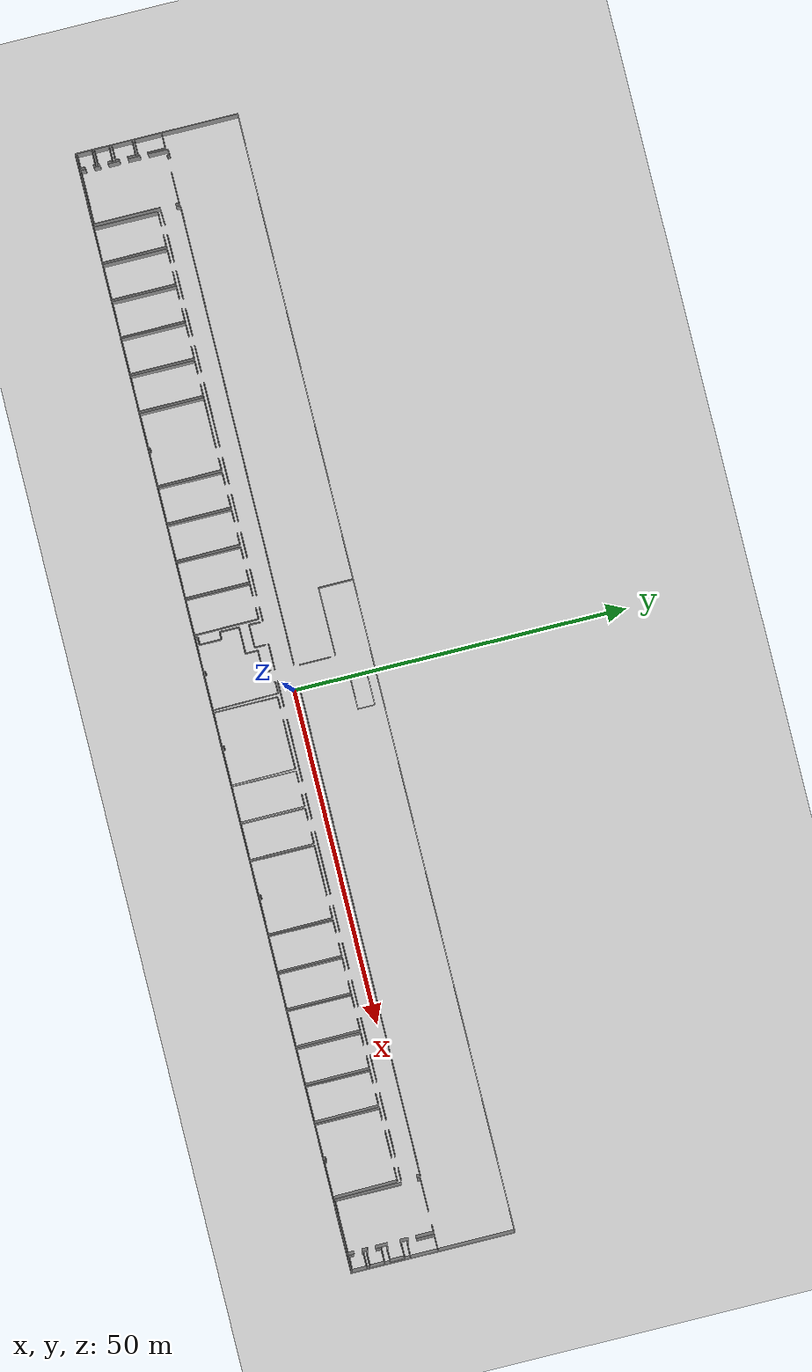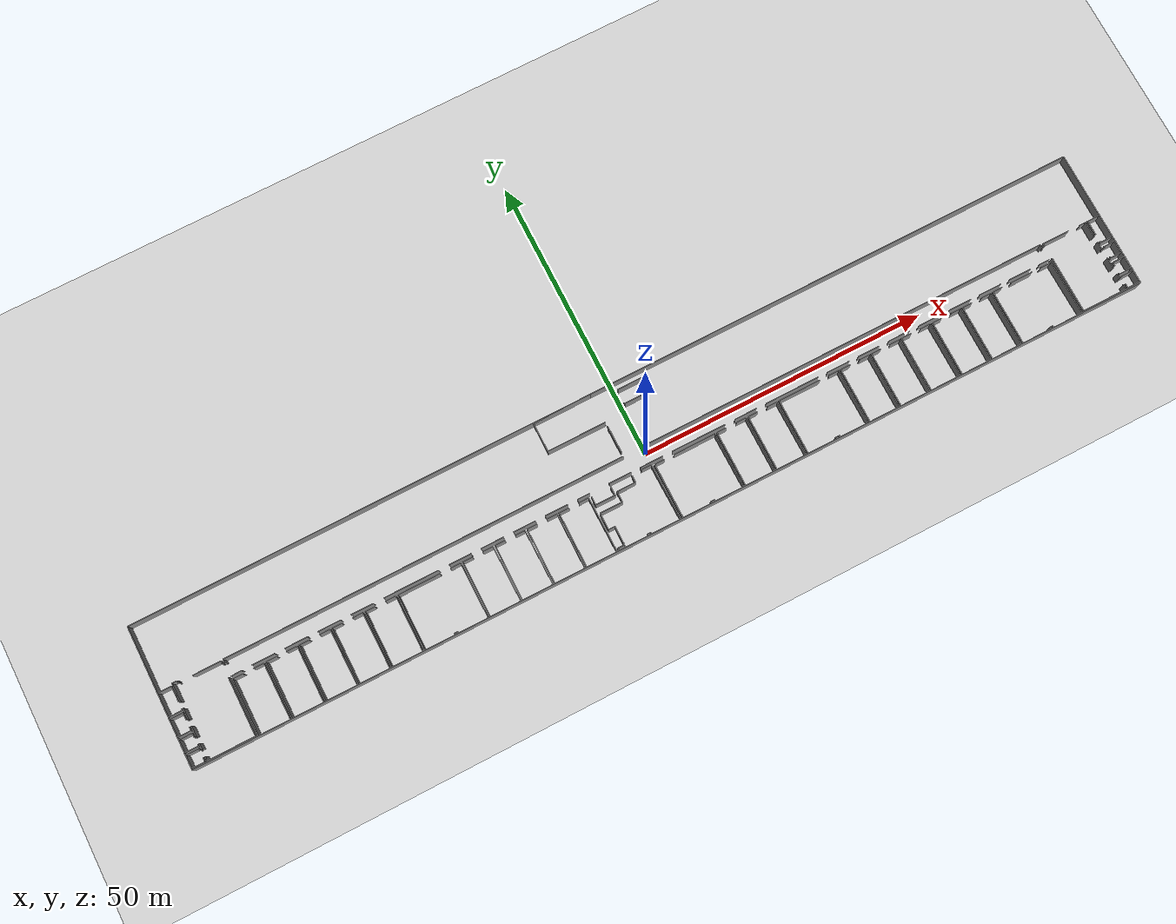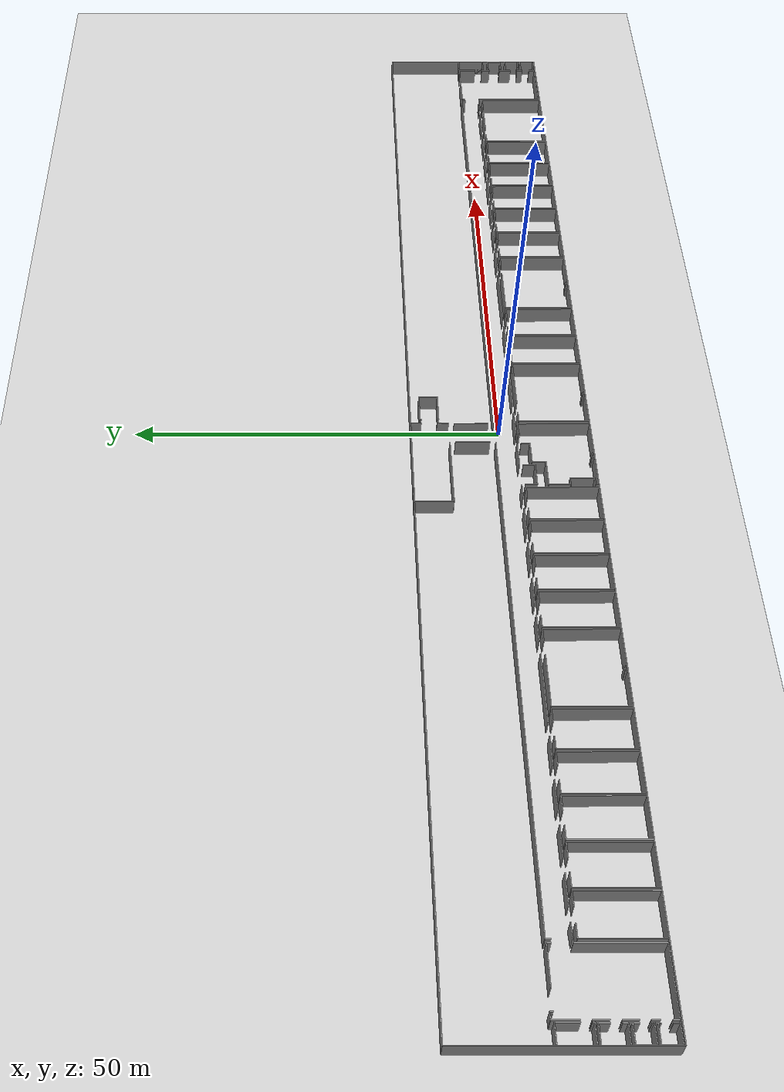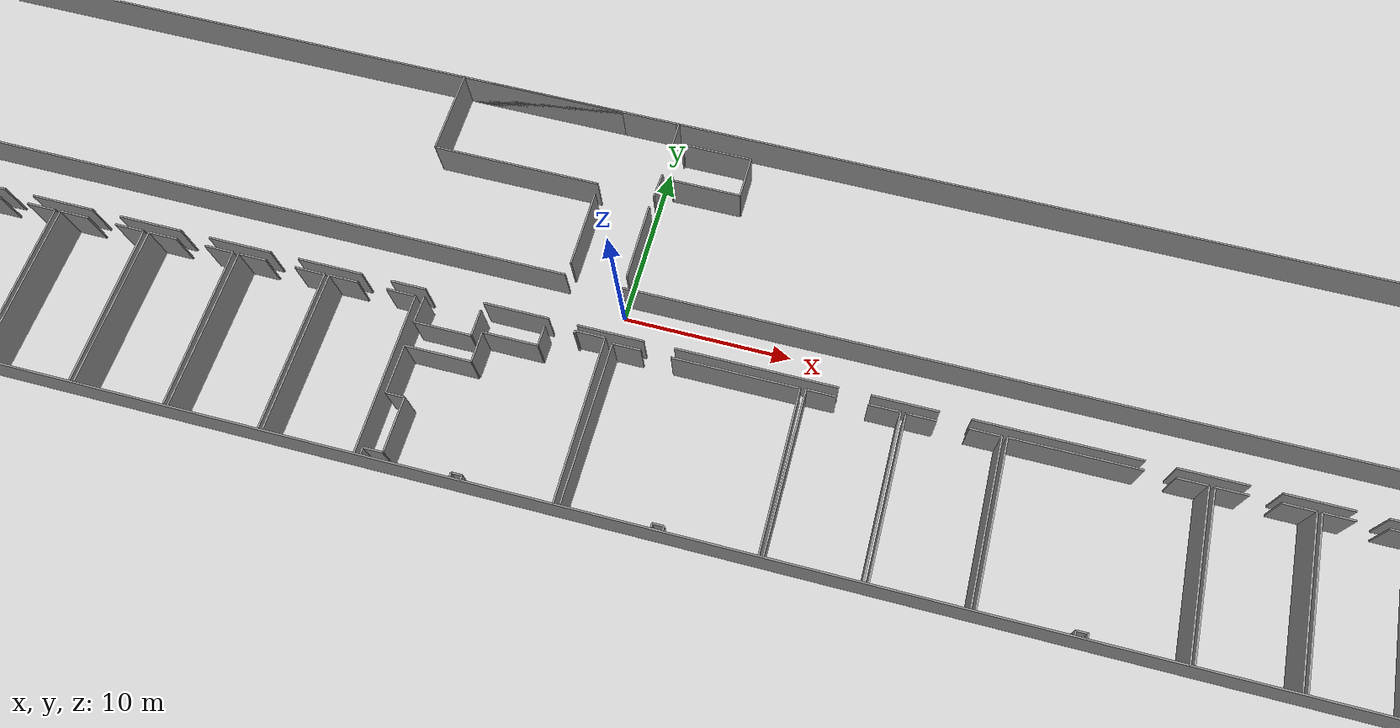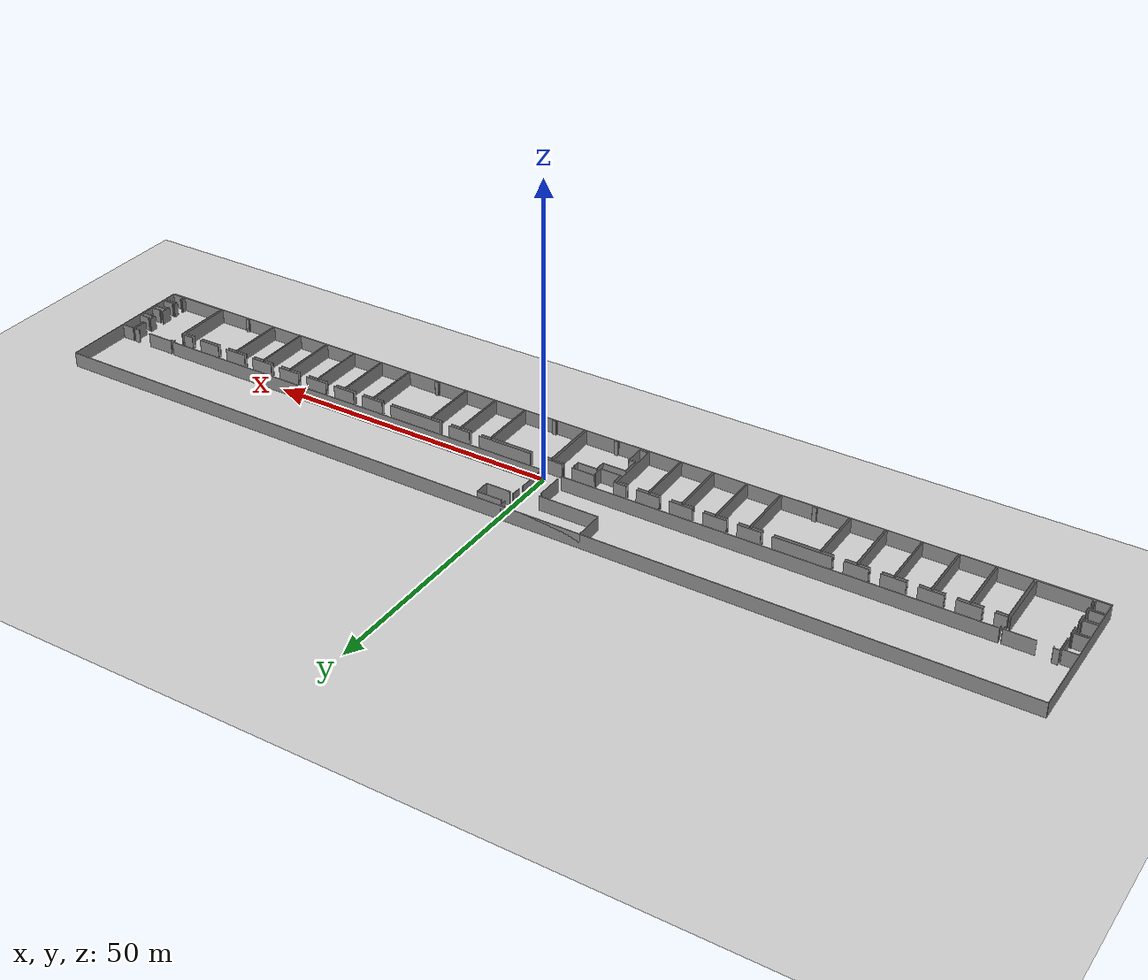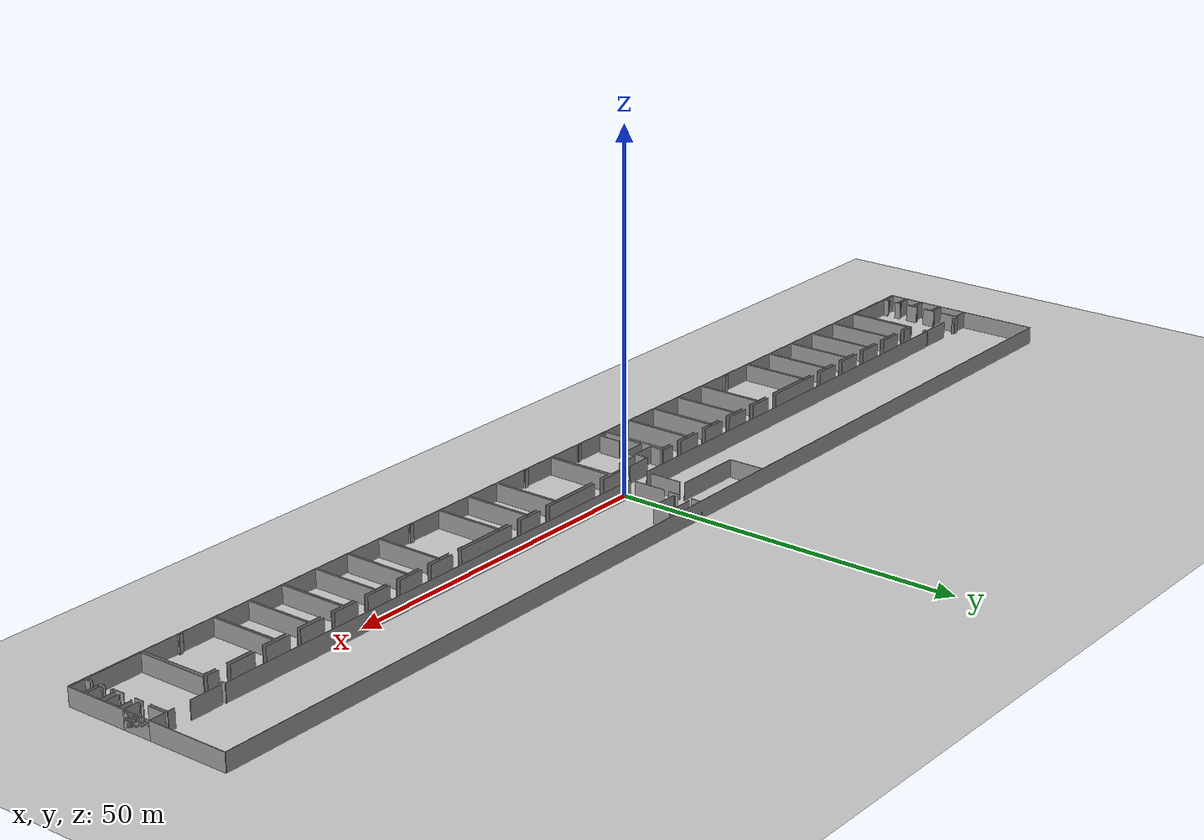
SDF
<sdf version="1.6">
  <world name="default">
    <light name="sun" type="directional">
      <cast_shadows>1</cast_shadows>
      <pose frame="">0 0 10 0 -0 0</pose>
      <diffuse>0.8 0.8 0.8 1</diffuse>
      <specular>0.1 0.1 0.1 1</specular>
      <attenuation>
        <range>1000</range>
        <constant>0.9</constant>
        <linear>0.01</linear>
        <quadratic>0.001</quadratic>
      </attenuation>
      <direction>-0.5 0.5 -1</direction>
    </light>
    <model name="ground_plane">
      <static>1</static>
      <link name="link">
        <collision name="collision">
          <geometry>
            <plane>
              <normal>0 0 1</normal>
              <size>100 100</size>
            </plane>
          </geometry>
          <surface>
            <friction>
              <ode>
                <mu>100</mu>
                <mu2>50</mu2>
              </ode>
              <torsional>
                <ode />
              </torsional>
            </friction>
            <contact>
              <ode />
            </contact>
            <bounce />
          </surface>
          <max_contacts>10</max_contacts>
        </collision>
        <visual name="visual">
          <cast_shadows>0</cast_shadows>
          <geometry>
            <plane>
              <normal>0 0 1</normal>
              <size>100 100</size>
            </plane>
          </geometry>
          <material>
            <script>
              <uri>file://media/materials/scripts/gazebo.material</uri>
              <name>Gazebo/Grey</name>
            </script>
          </material>
        </visual>
        <self_collide>0</self_collide>
        <kinematic>0</kinematic>
        <gravity>1</gravity>
      </link>
    </model>
    <gravity>0 0 -9.8</gravity>
    <magnetic_field>6e-06 2.3e-05 -4.2e-05</magnetic_field>
    <atmosphere type="adiabatic" />
    <physics default="0" name="default_physics" type="ode">
      <max_step_size>0.001</max_step_size>
      <real_time_factor>1</real_time_factor>
      <real_time_update_rate>1000</real_time_update_rate>
    </physics>
    <scene>
      <ambient>0.4 0.4 0.4 1</ambient>
      <background>0.7 0.7 0.7 1</background>
      <shadows>1</shadows>
    </scene>
    <spherical_coordinates>
      <surface_model>EARTH_WGS84</surface_model>
      <latitude_deg>0</latitude_deg>
      <longitude_deg>0</longitude_deg>
      <elevation>0</elevation>
      <heading_deg>0</heading_deg>
    </spherical_coordinates>
  <model name="0510045907_A_40_1_105">
		<static>1</static>
		<link name="Wall_0">
			<collision name="Wall_0_Collision">
				<geometry>
					<box>
						<size>9.99086016045 0.1 2.5</size>
					</box>
				</geometry>
				<pose frame="">4.99543008023 0 1.25 0 0 0</pose>
			</collision>
			<visual name="Wall_0_Visual">
				<pose frame="">4.99543008023 0 1.25 0 0 0</pose>
				<geometry>
					<box>
						<size>9.99086016045 0.1 2.5</size>
					</box>
				</geometry>
				<material>
					<script>
						<uri>file://media/materials/scripts/gazebo.material</uri>
						<name>Gazebo/Grey</name>
					</script>
					<ambient>1 1 1 1</ambient>
				</material>
			</visual>
			<pose frame="">10.6052604854 -24.2655123388 0 0 0 1.57079632679</pose>
		</link>
		<link name="Wall_1">
			<collision name="Wall_1_Collision">
				<geometry>
					<box>
						<size>0.518178125317 0.1 2.5</size>
					</box>
				</geometry>
				<pose frame="">0.259089062659 0 1.25 0 0 0</pose>
			</collision>
			<visual name="Wall_1_Visual">
				<pose frame="">0.259089062659 0 1.25 0 0 0</pose>
				<geometry>
					<box>
						<size>0.518178125317 0.1 2.5</size>
					</box>
				</geometry>
				<material>
					<script>
						<uri>file://media/materials/scripts/gazebo.material</uri>
						<name>Gazebo/Grey</name>
					</script>
					<ambient>1 1 1 1</ambient>
				</material>
			</visual>
			<pose frame="">10.6052604854 -11.9739514573 0 0 0 1.57079632679</pose>
		</link>
		<link name="Wall_2">
			<collision name="Wall_2_Collision">
				<geometry>
					<box>
						<size>4.76109474967 0.1 2.5</size>
					</box>
				</geometry>
				<pose frame="">2.38054737483 0 1.25 0 0 0</pose>
			</collision>
			<visual name="Wall_2_Visual">
				<pose frame="">2.38054737483 0 1.25 0 0 0</pose>
				<geometry>
					<box>
						<size>4.76109474967 0.1 2.5</size>
					</box>
				</geometry>
				<material>
					<script>
						<uri>file://media/materials/scripts/gazebo.material</uri>
						<name>Gazebo/Grey</name>
					</script>
					<ambient>1 1 1 1</ambient>
				</material>
			</visual>
			<pose frame="">10.6052604854 -11.455773332 0 0 0 3.14159265359</pose>
		</link>
		<link name="Wall_3">
			<collision name="Wall_3_Collision">
				<geometry>
					<box>
						<size>0.101553772723 0.1 2.5</size>
					</box>
				</geometry>
				<pose frame="">0.0507768863613 0 1.25 0 0 0</pose>
			</collision>
			<visual name="Wall_3_Visual">
				<pose frame="">0.0507768863613 0 1.25 0 0 0</pose>
				<geometry>
					<box>
						<size>0.101553772723 0.1 2.5</size>
					</box>
				</geometry>
				<material>
					<script>
						<uri>file://media/materials/scripts/gazebo.material</uri>
						<name>Gazebo/Grey</name>
					</script>
					<ambient>1 1 1 1</ambient>
				</material>
			</visual>
			<pose frame="">3.5361023662 -11.455773332 0 0 0 3.14159265359</pose>
		</link>
		<link name="Wall_4">
			<collision name="Wall_4_Collision">
				<geometry>
					<box>
						<size>0.338174063166 0.1 2.5</size>
					</box>
				</geometry>
				<pose frame="">0.169087031583 0 1.25 0 0 0</pose>
			</collision>
			<visual name="Wall_4_Visual">
				<pose frame="">0.169087031583 0 1.25 0 0 0</pose>
				<geometry>
					<box>
						<size>0.338174063166 0.1 2.5</size>
					</box>
				</geometry>
				<material>
					<script>
						<uri>file://media/materials/scripts/gazebo.material</uri>
						<name>Gazebo/Grey</name>
					</script>
					<ambient>1 1 1 1</ambient>
				</material>
			</visual>
			<pose frame="">3.43454859348 -11.455773332 0 0 0 1.57079632679</pose>
		</link>
		<link name="Wall_5">
			<collision name="Wall_5_Collision">
				<geometry>
					<box>
						<size>0.868030872347 0.1 2.5</size>
					</box>
				</geometry>
				<pose frame="">0.434015436173 0 1.25 0 0 0</pose>
			</collision>
			<visual name="Wall_5_Visual">
				<pose frame="">0.434015436173 0 1.25 0 0 0</pose>
				<geometry>
					<box>
						<size>0.868030872347 0.1 2.5</size>
					</box>
				</geometry>
				<material>
					<script>
						<uri>file://media/materials/scripts/gazebo.material</uri>
						<name>Gazebo/Grey</name>
					</script>
					<ambient>1 1 1 1</ambient>
				</material>
			</visual>
			<pose frame="">3.43454859348 -11.1175992688 0 0 0 3.14159265359</pose>
		</link>
		<link name="Wall_6">
			<collision name="Wall_6_Collision">
				<geometry>
					<box>
						<size>3.02985680918 0.1 2.5</size>
					</box>
				</geometry>
				<pose frame="">1.51492840459 0 1.25 0 0 0</pose>
			</collision>
			<visual name="Wall_6_Visual">
				<pose frame="">1.51492840459 0 1.25 0 0 0</pose>
				<geometry>
					<box>
						<size>3.02985680918 0.1 2.5</size>
					</box>
				</geometry>
				<material>
					<script>
						<uri>file://media/materials/scripts/gazebo.material</uri>
						<name>Gazebo/Grey</name>
					</script>
					<ambient>1 1 1 1</ambient>
				</material>
			</visual>
			<pose frame="">2.56651772113 -11.1175992688 0 0 0 -1.57079632679</pose>
		</link>
		<link name="Wall_7">
			<collision name="Wall_7_Collision">
				<geometry>
					<box>
						<size>1.83279171321 0.1 2.5</size>
					</box>
				</geometry>
				<pose frame="">0.916395856606 0 1.25 0 0 0</pose>
			</collision>
			<visual name="Wall_7_Visual">
				<pose frame="">0.916395856606 0 1.25 0 0 0</pose>
				<geometry>
					<box>
						<size>1.83279171321 0.1 2.5</size>
					</box>
				</geometry>
				<material>
					<script>
						<uri>file://media/materials/scripts/gazebo.material</uri>
						<name>Gazebo/Grey</name>
					</script>
					<ambient>1 1 1 1</ambient>
				</material>
			</visual>
			<pose frame="">2.56651772113 -15.3219254595 0 0 0 -1.57079632679</pose>
		</link>
		<link name="Wall_8">
			<collision name="Wall_8_Collision">
				<geometry>
					<box>
						<size>1.76728952981 0.1 2.5</size>
					</box>
				</geometry>
				<pose frame="">0.883644764903 0 1.25 0 0 0</pose>
			</collision>
			<visual name="Wall_8_Visual">
				<pose frame="">0.883644764903 0 1.25 0 0 0</pose>
				<geometry>
					<box>
						<size>1.76728952981 0.1 2.5</size>
					</box>
				</geometry>
				<material>
					<script>
						<uri>file://media/materials/scripts/gazebo.material</uri>
						<name>Gazebo/Grey</name>
					</script>
					<ambient>1 1 1 1</ambient>
				</material>
			</visual>
			<pose frame="">2.56651772113 -18.3621915304 0 0 0 -1.57079632679</pose>
		</link>
		<link name="Wall_9">
			<collision name="Wall_9_Collision">
				<geometry>
					<box>
						<size>0.966030263024 0.1 2.5</size>
					</box>
				</geometry>
				<pose frame="">0.483015131512 0 1.25 0 0 0</pose>
			</collision>
			<visual name="Wall_9_Visual">
				<pose frame="">0.483015131512 0 1.25 0 0 0</pose>
				<geometry>
					<box>
						<size>0.966030263024 0.1 2.5</size>
					</box>
				</geometry>
				<material>
					<script>
						<uri>file://media/materials/scripts/gazebo.material</uri>
						<name>Gazebo/Grey</name>
					</script>
					<ambient>1 1 1 1</ambient>
				</material>
			</visual>
			<pose frame="">2.56651772113 -21.2927795268 0 0 0 -1.57079632679</pose>
		</link>
		<link name="Wall_10">
			<collision name="Wall_10_Collision">
				<geometry>
					<box>
						<size>0.763684370874 0.1 2.5</size>
					</box>
				</geometry>
				<pose frame="">0.381842185437 0 1.25 0 0 0</pose>
			</collision>
			<visual name="Wall_10_Visual">
				<pose frame="">0.381842185437 0 1.25 0 0 0</pose>
				<geometry>
					<box>
						<size>0.763684370874 0.1 2.5</size>
					</box>
				</geometry>
				<material>
					<script>
						<uri>file://media/materials/scripts/gazebo.material</uri>
						<name>Gazebo/Grey</name>
					</script>
					<ambient>1 1 1 1</ambient>
				</material>
			</visual>
			<pose frame="">2.56651772113 -23.4822788667 0 0 0 -1.57079632679</pose>
		</link>
		<link name="Wall_11">
			<collision name="Wall_11_Collision">
				<geometry>
					<box>
						<size>8.0387665346 0.1 2.5</size>
					</box>
				</geometry>
				<pose frame="">4.0193832673 0 1.25 0 0 0</pose>
			</collision>
			<visual name="Wall_11_Visual">
				<pose frame="">4.0193832673 0 1.25 0 0 0</pose>
				<geometry>
					<box>
						<size>8.0387665346 0.1 2.5</size>
					</box>
				</geometry>
				<material>
					<script>
						<uri>file://media/materials/scripts/gazebo.material</uri>
						<name>Gazebo/Grey</name>
					</script>
					<ambient>1 1 1 1</ambient>
				</material>
			</visual>
			<pose frame="">2.56651772113 -24.2459632375 0 0 0 -0.00243185573727</pose>
		</link>
		<link name="Wall_12">
			<collision name="Wall_12_Collision">
				<geometry>
					<box>
						<size>2.32431197319 0.1 2.5</size>
					</box>
				</geometry>
				<pose frame="">1.16215598659 0 1.25 0 0 0</pose>
			</collision>
			<visual name="Wall_12_Visual">
				<pose frame="">1.16215598659 0 1.25 0 0 0</pose>
				<geometry>
					<box>
						<size>2.32431197319 0.1 2.5</size>
					</box>
				</geometry>
				<material>
					<script>
						<uri>file://media/materials/scripts/gazebo.material</uri>
						<name>Gazebo/Grey</name>
					</script>
					<ambient>1 1 1 1</ambient>
				</material>
			</visual>
			<pose frame="">0.0215801767036 -15.5831725399 0 0 0 0.0</pose>
		</link>
		<link name="Wall_13">
			<collision name="Wall_13_Collision">
				<geometry>
					<box>
						<size>0.259469889306 0.1 2.5</size>
					</box>
				</geometry>
				<pose frame="">0.129734944653 0 1.25 0 0 0</pose>
			</collision>
			<visual name="Wall_13_Visual">
				<pose frame="">0.129734944653 0 1.25 0 0 0</pose>
				<geometry>
					<box>
						<size>0.259469889306 0.1 2.5</size>
					</box>
				</geometry>
				<material>
					<script>
						<uri>file://media/materials/scripts/gazebo.material</uri>
						<name>Gazebo/Grey</name>
					</script>
					<ambient>1 1 1 1</ambient>
				</material>
			</visual>
			<pose frame="">2.34589214989 -15.5831725399 0 0 0 1.57079632679</pose>
		</link>
		<link name="Wall_14">
			<collision name="Wall_14_Collision">
				<geometry>
					<box>
						<size>2.67086422261 0.1 2.5</size>
					</box>
				</geometry>
				<pose frame="">1.3354321113 0 1.25 0 0 0</pose>
			</collision>
			<visual name="Wall_14_Visual">
				<pose frame="">1.3354321113 0 1.25 0 0 0</pose>
				<geometry>
					<box>
						<size>2.67086422261 0.1 2.5</size>
					</box>
				</geometry>
				<material>
					<script>
						<uri>file://media/materials/scripts/gazebo.material</uri>
						<name>Gazebo/Grey</name>
					</script>
					<ambient>1 1 1 1</ambient>
				</material>
			</visual>
			<pose frame="">2.34589214989 -14.1477099624 0 0 0 1.57079632679</pose>
		</link>
		<link name="Wall_15">
			<collision name="Wall_15_Collision">
				<geometry>
					<box>
						<size>2.33726007921 0.1 2.5</size>
					</box>
				</geometry>
				<pose frame="">1.16863003961 0 1.25 0 0 0</pose>
			</collision>
			<visual name="Wall_15_Visual">
				<pose frame="">1.16863003961 0 1.25 0 0 0</pose>
				<geometry>
					<box>
						<size>2.33726007921 0.1 2.5</size>
					</box>
				</geometry>
				<material>
					<script>
						<uri>file://media/materials/scripts/gazebo.material</uri>
						<name>Gazebo/Grey</name>
					</script>
					<ambient>1 1 1 1</ambient>
				</material>
			</visual>
			<pose frame="">2.34589214989 -11.4768457398 0 0 0 3.14159265359</pose>
		</link>
		<link name="Wall_16">
			<collision name="Wall_16_Collision">
				<geometry>
					<box>
						<size>4.10634721403 0.1 2.5</size>
					</box>
				</geometry>
				<pose frame="">2.05317360702 0 1.25 0 0 0</pose>
			</collision>
			<visual name="Wall_16_Visual">
				<pose frame="">2.05317360702 0 1.25 0 0 0</pose>
				<geometry>
					<box>
						<size>4.10634721403 0.1 2.5</size>
					</box>
				</geometry>
				<material>
					<script>
						<uri>file://media/materials/scripts/gazebo.material</uri>
						<name>Gazebo/Grey</name>
					</script>
					<ambient>1 1 1 1</ambient>
				</material>
			</visual>
			<pose frame="">0.00863207068143 -11.4768457398 0 0 0 -1.56764312839</pose>
		</link>
		<link name="Wall_17">
			<collision name="Wall_17_Collision">
				<geometry>
					<box>
						<size>2.24687722149 0.1 2.5</size>
					</box>
				</geometry>
				<pose frame="">1.12343861074 0 1.25 0 0 0</pose>
			</collision>
			<visual name="Wall_17_Visual">
				<pose frame="">1.12343861074 0 1.25 0 0 0</pose>
				<geometry>
					<box>
						<size>2.24687722149 0.1 2.5</size>
					</box>
				</geometry>
				<material>
					<script>
						<uri>file://media/materials/scripts/gazebo.material</uri>
						<name>Gazebo/Grey</name>
					</script>
					<ambient>1 1 1 1</ambient>
				</material>
			</visual>
			<pose frame="">0.013201990454 -18.9702447446 0 0 0 0.0</pose>
		</link>
		<link name="Wall_18">
			<collision name="Wall_18_Collision">
				<geometry>
					<box>
						<size>0.593327917132 0.1 2.5</size>
					</box>
				</geometry>
				<pose frame="">0.296663958566 0 1.25 0 0 0</pose>
			</collision>
			<visual name="Wall_18_Visual">
				<pose frame="">0.296663958566 0 1.25 0 0 0</pose>
				<geometry>
					<box>
						<size>0.593327917132 0.1 2.5</size>
					</box>
				</geometry>
				<material>
					<script>
						<uri>file://media/materials/scripts/gazebo.material</uri>
						<name>Gazebo/Grey</name>
					</script>
					<ambient>1 1 1 1</ambient>
				</material>
			</visual>
			<pose frame="">2.26007921194 -18.9702447446 0 0 0 1.57079632679</pose>
		</link>
		<link name="Wall_19">
			<collision name="Wall_19_Collision">
				<geometry>
					<box>
						<size>1.24073321824 0.1 2.5</size>
					</box>
				</geometry>
				<pose frame="">0.62036660912 0 1.25 0 0 0</pose>
			</collision>
			<visual name="Wall_19_Visual">
				<pose frame="">0.62036660912 0 1.25 0 0 0</pose>
				<geometry>
					<box>
						<size>1.24073321824 0.1 2.5</size>
					</box>
				</geometry>
				<material>
					<script>
						<uri>file://media/materials/scripts/gazebo.material</uri>
						<name>Gazebo/Grey</name>
					</script>
					<ambient>1 1 1 1</ambient>
				</material>
			</visual>
			<pose frame="">2.26007921194 -17.1638570123 0 0 0 1.57079632679</pose>
		</link>
		<link name="Wall_20">
			<collision name="Wall_20_Collision">
				<geometry>
					<box>
						<size>2.26007921194 0.1 2.5</size>
					</box>
				</geometry>
				<pose frame="">1.13003960597 0 1.25 0 0 0</pose>
			</collision>
			<visual name="Wall_20_Visual">
				<pose frame="">1.13003960597 0 1.25 0 0 0</pose>
				<geometry>
					<box>
						<size>2.26007921194 0.1 2.5</size>
					</box>
				</geometry>
				<material>
					<script>
						<uri>file://media/materials/scripts/gazebo.material</uri>
						<name>Gazebo/Grey</name>
					</script>
					<ambient>1 1 1 1</ambient>
				</material>
			</visual>
			<pose frame="">2.26007921194 -15.923123794 0 0 0 3.14159265359</pose>
		</link>
		<link name="Wall_21">
			<collision name="Wall_21_Collision">
				<geometry>
					<box>
						<size>3.04714954996 0.1 2.5</size>
					</box>
				</geometry>
				<pose frame="">1.52357477498 0 1.25 0 0 0</pose>
			</collision>
			<visual name="Wall_21_Visual">
				<pose frame="">1.52357477498 0 1.25 0 0 0</pose>
				<geometry>
					<box>
						<size>3.04714954996 0.1 2.5</size>
					</box>
				</geometry>
				<material>
					<script>
						<uri>file://media/materials/scripts/gazebo.material</uri>
						<name>Gazebo/Grey</name>
					</script>
					<ambient>1 1 1 1</ambient>
				</material>
			</visual>
			<pose frame="">0.0 -15.923123794 0 0 0 -1.56646374267</pose>
		</link>
		<link name="Wall_22">
			<collision name="Wall_22_Collision">
				<geometry>
					<box>
						<size>2.25931755865 0.1 2.5</size>
					</box>
				</geometry>
				<pose frame="">1.12965877932 0 1.25 0 0 0</pose>
			</collision>
			<visual name="Wall_22_Visual">
				<pose frame="">1.12965877932 0 1.25 0 0 0</pose>
				<geometry>
					<box>
						<size>2.25931755865 0.1 2.5</size>
					</box>
				</geometry>
				<material>
					<script>
						<uri>file://media/materials/scripts/gazebo.material</uri>
						<name>Gazebo/Grey</name>
					</script>
					<ambient>1 1 1 1</ambient>
				</material>
			</visual>
			<pose frame="">2.31034832944 -21.6083578755 0 0 0 3.14159265359</pose>
		</link>
		<link name="Wall_23">
			<collision name="Wall_23_Collision">
				<geometry>
					<box>
						<size>2.22148877831 0.1 2.5</size>
					</box>
				</geometry>
				<pose frame="">1.11074438915 0 1.25 0 0 0</pose>
			</collision>
			<visual name="Wall_23_Visual">
				<pose frame="">1.11074438915 0 1.25 0 0 0</pose>
				<geometry>
					<box>
						<size>2.22148877831 0.1 2.5</size>
					</box>
				</geometry>
				<material>
					<script>
						<uri>file://media/materials/scripts/gazebo.material</uri>
						<name>Gazebo/Grey</name>
					</script>
					<ambient>1 1 1 1</ambient>
				</material>
			</visual>
			<pose frame="">0.0510307707931 -21.6083578755 0 0 0 1.57079632679</pose>
		</link>
		<link name="Wall_24">
			<collision name="Wall_24_Collision">
				<geometry>
					<box>
						<size>2.20092413933 0.1 2.5</size>
					</box>
				</geometry>
				<pose frame="">1.10046206967 0 1.25 0 0 0</pose>
			</collision>
			<visual name="Wall_24_Visual">
				<pose frame="">1.10046206967 0 1.25 0 0 0</pose>
				<geometry>
					<box>
						<size>2.20092413933 0.1 2.5</size>
					</box>
				</geometry>
				<material>
					<script>
						<uri>file://media/materials/scripts/gazebo.material</uri>
						<name>Gazebo/Grey</name>
					</script>
					<ambient>1 1 1 1</ambient>
				</material>
			</visual>
			<pose frame="">0.0510307707931 -19.3868690972 0 0 0 0.0</pose>
		</link>
		<link name="Wall_25">
			<collision name="Wall_25_Collision">
				<geometry>
					<box>
						<size>0.742104194171 0.1 2.5</size>
					</box>
				</geometry>
				<pose frame="">0.371052097085 0 1.25 0 0 0</pose>
			</collision>
			<visual name="Wall_25_Visual">
				<pose frame="">0.371052097085 0 1.25 0 0 0</pose>
				<geometry>
					<box>
						<size>0.742104194171 0.1 2.5</size>
					</box>
				</geometry>
				<material>
					<script>
						<uri>file://media/materials/scripts/gazebo.material</uri>
						<name>Gazebo/Grey</name>
					</script>
					<ambient>1 1 1 1</ambient>
				</material>
			</visual>
			<pose frame="">2.25195491012 -19.3868690972 0 0 0 -1.57079632679</pose>
		</link>
		<link name="Wall_26">
			<collision name="Wall_26_Collision">
				<geometry>
					<box>
						<size>0.259028818743 0.1 2.5</size>
					</box>
				</geometry>
				<pose frame="">0.129514409372 0 1.25 0 0 0</pose>
			</collision>
			<visual name="Wall_26_Visual">
				<pose frame="">0.129514409372 0 1.25 0 0 0</pose>
				<geometry>
					<box>
						<size>0.259028818743 0.1 2.5</size>
					</box>
				</geometry>
				<material>
					<script>
						<uri>file://media/materials/scripts/gazebo.material</uri>
						<name>Gazebo/Grey</name>
					</script>
					<ambient>1 1 1 1</ambient>
				</material>
			</visual>
			<pose frame="">2.25195491012 -21.3559967503 0 0 0 -1.34340976209</pose>
		</link>
		<link name="Wall_27">
			<collision name="Wall_27_Collision">
				<geometry>
					<box>
						<size>0.731948816899 0.1 2.5</size>
					</box>
				</geometry>
				<pose frame="">0.365974408449 0 1.25 0 0 0</pose>
			</collision>
			<visual name="Wall_27_Visual">
				<pose frame="">0.365974408449 0 1.25 0 0 0</pose>
				<geometry>
					<box>
						<size>0.731948816899 0.1 2.5</size>
					</box>
				</geometry>
				<material>
					<script>
						<uri>file://media/materials/scripts/gazebo.material</uri>
						<name>Gazebo/Grey</name>
					</script>
					<ambient>1 1 1 1</ambient>
				</material>
			</visual>
			<pose frame="">2.22199654717 -24.2337767848 0 0 0 1.57079632679</pose>
		</link>
		<link name="Wall_28">
			<collision name="Wall_28_Collision">
				<geometry>
					<box>
						<size>0.328272570326 0.1 2.5</size>
					</box>
				</geometry>
				<pose frame="">0.164136285163 0 1.25 0 0 0</pose>
			</collision>
			<visual name="Wall_28_Visual">
				<pose frame="">0.164136285163 0 1.25 0 0 0</pose>
				<geometry>
					<box>
						<size>0.328272570326 0.1 2.5</size>
					</box>
				</geometry>
				<material>
					<script>
						<uri>file://media/materials/scripts/gazebo.material</uri>
						<name>Gazebo/Grey</name>
					</script>
					<ambient>1 1 1 1</ambient>
				</material>
			</visual>
			<pose frame="">2.22199654717 -22.2900375749 0 0 0 1.57079632679</pose>
		</link>
		<link name="Wall_29">
			<collision name="Wall_29_Collision">
				<geometry>
					<box>
						<size>2.17096577638 0.1 2.5</size>
					</box>
				</geometry>
				<pose frame="">1.08548288819 0 1.25 0 0 0</pose>
			</collision>
			<visual name="Wall_29_Visual">
				<pose frame="">1.08548288819 0 1.25 0 0 0</pose>
				<geometry>
					<box>
						<size>2.17096577638 0.1 2.5</size>
					</box>
				</geometry>
				<material>
					<script>
						<uri>file://media/materials/scripts/gazebo.material</uri>
						<name>Gazebo/Grey</name>
					</script>
					<ambient>1 1 1 1</ambient>
				</material>
			</visual>
			<pose frame="">2.22199654717 -21.9617650046 0 0 0 3.14159265359</pose>
		</link>
		<link name="Wall_30">
			<collision name="Wall_30_Collision">
				<geometry>
					<box>
						<size>2.27201178024 0.1 2.5</size>
					</box>
				</geometry>
				<pose frame="">1.13600589012 0 1.25 0 0 0</pose>
			</collision>
			<visual name="Wall_30_Visual">
				<pose frame="">1.13600589012 0 1.25 0 0 0</pose>
				<geometry>
					<box>
						<size>2.27201178024 0.1 2.5</size>
					</box>
				</geometry>
				<material>
					<script>
						<uri>file://media/materials/scripts/gazebo.material</uri>
						<name>Gazebo/Grey</name>
					</script>
					<ambient>1 1 1 1</ambient>
				</material>
			</visual>
			<pose frame="">0.0510307707931 -21.9617650046 0 0 0 -1.57079632679</pose>
		</link>
		<link name="Wall_31">
			<collision name="Wall_31_Collision">
				<geometry>
					<box>
						<size>2.17096577638 0.1 2.5</size>
					</box>
				</geometry>
				<pose frame="">1.08548288819 0 1.25 0 0 0</pose>
			</collision>
			<visual name="Wall_31_Visual">
				<pose frame="">1.08548288819 0 1.25 0 0 0</pose>
				<geometry>
					<box>
						<size>2.17096577638 0.1 2.5</size>
					</box>
				</geometry>
				<material>
					<script>
						<uri>file://media/materials/scripts/gazebo.material</uri>
						<name>Gazebo/Grey</name>
					</script>
					<ambient>1 1 1 1</ambient>
				</material>
			</visual>
			<pose frame="">0.0510307707931 -24.2337767848 0 0 0 0.0</pose>
		</link>
		<link name="Wall_32">
			<collision name="Wall_32_Collision">
				<geometry>
					<box>
						<size>0.631156697471 0.1 2.5</size>
					</box>
				</geometry>
				<pose frame="">0.315578348736 0 1.25 0 0 0</pose>
			</collision>
			<visual name="Wall_32_Visual">
				<pose frame="">0.315578348736 0 1.25 0 0 0</pose>
				<geometry>
					<box>
						<size>0.631156697471 0.1 2.5</size>
					</box>
				</geometry>
				<material>
					<script>
						<uri>file://media/materials/scripts/gazebo.material</uri>
						<name>Gazebo/Grey</name>
					</script>
					<ambient>1 1 1 1</ambient>
				</material>
			</visual>
			<pose frame="">11.0272164111 -11.9899461765 0 0 0 1.57079632679</pose>
		</link>
		<link name="Wall_33">
			<collision name="Wall_33_Collision">
				<geometry>
					<box>
						<size>69.0507261095 0.1 2.5</size>
					</box>
				</geometry>
				<pose frame="">34.5253630547 0 1.25 0 0 0</pose>
			</collision>
			<visual name="Wall_33_Visual">
				<pose frame="">34.5253630547 0 1.25 0 0 0</pose>
				<geometry>
					<box>
						<size>69.0507261095 0.1 2.5</size>
					</box>
				</geometry>
				<material>
					<script>
						<uri>file://media/materials/scripts/gazebo.material</uri>
						<name>Gazebo/Grey</name>
					</script>
					<ambient>1 1 1 1</ambient>
				</material>
			</visual>
			<pose frame="">11.0272164111 -11.358789479 0 0 0 0.0</pose>
		</link>
		<link name="Wall_34">
			<collision name="Wall_34_Collision">
				<geometry>
					<box>
						<size>72.8135472733 0.1 2.5</size>
					</box>
				</geometry>
				<pose frame="">36.4067736366 0 1.25 0 0 0</pose>
			</collision>
			<visual name="Wall_34_Visual">
				<pose frame="">36.4067736366 0 1.25 0 0 0</pose>
				<geometry>
					<box>
						<size>72.8135472733 0.1 2.5</size>
					</box>
				</geometry>
				<material>
					<script>
						<uri>file://media/materials/scripts/gazebo.material</uri>
						<name>Gazebo/Grey</name>
					</script>
					<ambient>1 1 1 1</ambient>
				</material>
			</visual>
			<pose frame="">83.46069869 -11.358789479 0 0 0 0.0</pose>
		</link>
		<link name="Wall_35">
			<collision name="Wall_35_Collision">
				<geometry>
					<box>
						<size>0.593327917132 0.1 2.5</size>
					</box>
				</geometry>
				<pose frame="">0.296663958566 0 1.25 0 0 0</pose>
			</collision>
			<visual name="Wall_35_Visual">
				<pose frame="">0.296663958566 0 1.25 0 0 0</pose>
				<geometry>
					<box>
						<size>0.593327917132 0.1 2.5</size>
					</box>
				</geometry>
				<material>
					<script>
						<uri>file://media/materials/scripts/gazebo.material</uri>
						<name>Gazebo/Grey</name>
					</script>
					<ambient>1 1 1 1</ambient>
				</material>
			</visual>
			<pose frame="">156.274245963 -11.358789479 0 0 0 -1.57079632679</pose>
		</link>
		<link name="Wall_36">
			<collision name="Wall_36_Collision">
				<geometry>
					<box>
						<size>1.80004062151 0.1 2.5</size>
					</box>
				</geometry>
				<pose frame="">0.900020310755 0 1.25 0 0 0</pose>
			</collision>
			<visual name="Wall_36_Visual">
				<pose frame="">0.900020310755 0 1.25 0 0 0</pose>
				<geometry>
					<box>
						<size>1.80004062151 0.1 2.5</size>
					</box>
				</geometry>
				<material>
					<script>
						<uri>file://media/materials/scripts/gazebo.material</uri>
						<name>Gazebo/Grey</name>
					</script>
					<ambient>1 1 1 1</ambient>
				</material>
			</visual>
			<pose frame="">156.274245963 -14.2241291764 0 0 0 3.14159265359</pose>
		</link>
		<link name="Wall_37">
			<collision name="Wall_37_Collision">
				<geometry>
					<box>
						<size>3.85117294607 0.1 2.5</size>
					</box>
				</geometry>
				<pose frame="">1.92558647304 0 1.25 0 0 0</pose>
			</collision>
			<visual name="Wall_37_Visual">
				<pose frame="">1.92558647304 0 1.25 0 0 0</pose>
				<geometry>
					<box>
						<size>3.85117294607 0.1 2.5</size>
					</box>
				</geometry>
				<material>
					<script>
						<uri>file://media/materials/scripts/gazebo.material</uri>
						<name>Gazebo/Grey</name>
					</script>
					<ambient>1 1 1 1</ambient>
				</material>
			</visual>
			<pose frame="">152.759723774 -14.2241291764 0 0 0 3.14159265359</pose>
		</link>
		<link name="Wall_38">
			<collision name="Wall_38_Collision">
				<geometry>
					<box>
						<size>3.86132832335 0.1 2.5</size>
					</box>
				</geometry>
				<pose frame="">1.93066416167 0 1.25 0 0 0</pose>
			</collision>
			<visual name="Wall_38_Visual">
				<pose frame="">1.93066416167 0 1.25 0 0 0</pose>
				<geometry>
					<box>
						<size>3.86132832335 0.1 2.5</size>
					</box>
				</geometry>
				<material>
					<script>
						<uri>file://media/materials/scripts/gazebo.material</uri>
						<name>Gazebo/Grey</name>
					</script>
					<ambient>1 1 1 1</ambient>
				</material>
			</visual>
			<pose frame="">147.171219661 -14.2241291764 0 0 0 3.14159265359</pose>
		</link>
		<link name="Wall_39">
			<collision name="Wall_39_Collision">
				<geometry>
					<box>
						<size>3.90042652585 0.1 2.5</size>
					</box>
				</geometry>
				<pose frame="">1.95021326292 0 1.25 0 0 0</pose>
			</collision>
			<visual name="Wall_39_Visual">
				<pose frame="">1.95021326292 0 1.25 0 0 0</pose>
				<geometry>
					<box>
						<size>3.90042652585 0.1 2.5</size>
					</box>
				</geometry>
				<material>
					<script>
						<uri>file://media/materials/scripts/gazebo.material</uri>
						<name>Gazebo/Grey</name>
					</script>
					<ambient>1 1 1 1</ambient>
				</material>
			</visual>
			<pose frame="">141.612927795 -14.2241291764 0 0 0 3.14159265359</pose>
		</link>
		<link name="Wall_40">
			<collision name="Wall_40_Collision">
				<geometry>
					<box>
						<size>3.91616736062 0.1 2.5</size>
					</box>
				</geometry>
				<pose frame="">1.95808368031 0 1.25 0 0 0</pose>
			</collision>
			<visual name="Wall_40_Visual">
				<pose frame="">1.95808368031 0 1.25 0 0 0</pose>
				<geometry>
					<box>
						<size>3.91616736062 0.1 2.5</size>
					</box>
				</geometry>
				<material>
					<script>
						<uri>file://media/materials/scripts/gazebo.material</uri>
						<name>Gazebo/Grey</name>
					</script>
					<ambient>1 1 1 1</ambient>
				</material>
			</visual>
			<pose frame="">135.995988626 -14.2241291764 0 0 0 3.14159265359</pose>
		</link>
		<link name="Wall_41">
			<collision name="Wall_41_Collision">
				<geometry>
					<box>
						<size>3.89027114857 0.1 2.5</size>
					</box>
				</geometry>
				<pose frame="">1.94513557429 0 1.25 0 0 0</pose>
			</collision>
			<visual name="Wall_41_Visual">
				<pose frame="">1.94513557429 0 1.25 0 0 0</pose>
				<geometry>
					<box>
						<size>3.89027114857 0.1 2.5</size>
					</box>
				</geometry>
				<material>
					<script>
						<uri>file://media/materials/scripts/gazebo.material</uri>
						<name>Gazebo/Grey</name>
					</script>
					<ambient>1 1 1 1</ambient>
				</material>
			</visual>
			<pose frame="">130.376256728 -14.2241291764 0 0 0 3.14159265359</pose>
		</link>
		<link name="Wall_42">
			<collision name="Wall_42_Collision">
				<geometry>
					<box>
						<size>3.87554585153 0.1 2.5</size>
					</box>
				</geometry>
				<pose frame="">1.93777292576 0 1.25 0 0 0</pose>
			</collision>
			<visual name="Wall_42_Visual">
				<pose frame="">1.93777292576 0 1.25 0 0 0</pose>
				<geometry>
					<box>
						<size>3.87554585153 0.1 2.5</size>
					</box>
				</geometry>
				<material>
					<script>
						<uri>file://media/materials/scripts/gazebo.material</uri>
						<name>Gazebo/Grey</name>
					</script>
					<ambient>1 1 1 1</ambient>
				</material>
			</visual>
			<pose frame="">124.787498731 -14.2241291764 0 0 0 3.14159265359</pose>
		</link>
		<link name="Wall_43">
			<collision name="Wall_43_Collision">
				<geometry>
					<box>
						<size>3.93952472834 0.1 2.5</size>
					</box>
				</geometry>
				<pose frame="">1.96976236417 0 1.25 0 0 0</pose>
			</collision>
			<visual name="Wall_43_Visual">
				<pose frame="">1.96976236417 0 1.25 0 0 0</pose>
				<geometry>
					<box>
						<size>3.93952472834 0.1 2.5</size>
					</box>
				</geometry>
				<material>
					<script>
						<uri>file://media/materials/scripts/gazebo.material</uri>
						<name>Gazebo/Grey</name>
					</script>
					<ambient>1 1 1 1</ambient>
				</material>
			</visual>
			<pose frame="">119.219305372 -14.2241291764 0 0 0 3.14159265359</pose>
		</link>
		<link name="Wall_44">
			<collision name="Wall_44_Collision">
				<geometry>
					<box>
						<size>9.44830912968 0.1 2.5</size>
					</box>
				</geometry>
				<pose frame="">4.72415456484 0 1.25 0 0 0</pose>
			</collision>
			<visual name="Wall_44_Visual">
				<pose frame="">4.72415456484 0 1.25 0 0 0</pose>
				<geometry>
					<box>
						<size>9.44830912968 0.1 2.5</size>
					</box>
				</geometry>
				<material>
					<script>
						<uri>file://media/materials/scripts/gazebo.material</uri>
						<name>Gazebo/Grey</name>
					</script>
					<ambient>1 1 1 1</ambient>
				</material>
			</visual>
			<pose frame="">113.61023662 -14.2241291764 0 0 0 3.14159265359</pose>
		</link>
		<link name="Wall_45">
			<collision name="Wall_45_Collision">
				<geometry>
					<box>
						<size>3.83924037778 0.1 2.5</size>
					</box>
				</geometry>
				<pose frame="">1.91962018889 0 1.25 0 0 0</pose>
			</collision>
			<visual name="Wall_45_Visual">
				<pose frame="">1.91962018889 0 1.25 0 0 0</pose>
				<geometry>
					<box>
						<size>3.83924037778 0.1 2.5</size>
					</box>
				</geometry>
				<material>
					<script>
						<uri>file://media/materials/scripts/gazebo.material</uri>
						<name>Gazebo/Grey</name>
					</script>
					<ambient>1 1 1 1</ambient>
				</material>
			</visual>
			<pose frame="">102.392353001 -14.2241291764 0 0 0 3.14159265359</pose>
		</link>
		<link name="Wall_46">
			<collision name="Wall_46_Collision">
				<geometry>
					<box>
						<size>9.38153752412 0.1 2.5</size>
					</box>
				</geometry>
				<pose frame="">4.69076876206 0 1.25 0 0 0</pose>
			</collision>
			<visual name="Wall_46_Visual">
				<pose frame="">4.69076876206 0 1.25 0 0 0</pose>
				<geometry>
					<box>
						<size>9.38153752412 0.1 2.5</size>
					</box>
				</geometry>
				<material>
					<script>
						<uri>file://media/materials/scripts/gazebo.material</uri>
						<name>Gazebo/Grey</name>
					</script>
					<ambient>1 1 1 1</ambient>
				</material>
			</visual>
			<pose frame="">96.7500253884 -14.2241291764 0 0 0 3.14159265359</pose>
		</link>
		<link name="Wall_47">
			<collision name="Wall_47_Collision">
				<geometry>
					<box>
						<size>3.90042652585 0.1 2.5</size>
					</box>
				</geometry>
				<pose frame="">1.95021326292 0 1.25 0 0 0</pose>
			</collision>
			<visual name="Wall_47_Visual">
				<pose frame="">1.95021326292 0 1.25 0 0 0</pose>
				<geometry>
					<box>
						<size>3.90042652585 0.1 2.5</size>
					</box>
				</geometry>
				<material>
					<script>
						<uri>file://media/materials/scripts/gazebo.material</uri>
						<name>Gazebo/Grey</name>
					</script>
					<ambient>1 1 1 1</ambient>
				</material>
			</visual>
			<pose frame="">85.5940895704 -14.2241291764 0 0 0 3.14159265359</pose>
		</link>
		<link name="Wall_48">
			<collision name="Wall_48_Collision">
				<geometry>
					<box>
						<size>3.86615212755 0.1 2.5</size>
					</box>
				</geometry>
				<pose frame="">1.93307606378 0 1.25 0 0 0</pose>
			</collision>
			<visual name="Wall_48_Visual">
				<pose frame="">1.93307606378 0 1.25 0 0 0</pose>
				<geometry>
					<box>
						<size>3.86615212755 0.1 2.5</size>
					</box>
				</geometry>
				<material>
					<script>
						<uri>file://media/materials/scripts/gazebo.material</uri>
						<name>Gazebo/Grey</name>
					</script>
					<ambient>1 1 1 1</ambient>
				</material>
			</visual>
			<pose frame="">80.0167563725 -14.2241291764 0 0 0 3.14159265359</pose>
		</link>
		<link name="Wall_49">
			<collision name="Wall_49_Collision">
				<geometry>
					<box>
						<size>2.10343251752 0.1 2.5</size>
					</box>
				</geometry>
				<pose frame="">1.05171625876 0 1.25 0 0 0</pose>
			</collision>
			<visual name="Wall_49_Visual">
				<pose frame="">1.05171625876 0 1.25 0 0 0</pose>
				<geometry>
					<box>
						<size>2.10343251752 0.1 2.5</size>
					</box>
				</geometry>
				<material>
					<script>
						<uri>file://media/materials/scripts/gazebo.material</uri>
						<name>Gazebo/Grey</name>
					</script>
					<ambient>1 1 1 1</ambient>
				</material>
			</visual>
			<pose frame="">72.6784807556 -14.2241291764 0 0 0 3.14159265359</pose>
		</link>
		<link name="Wall_50">
			<collision name="Wall_50_Collision">
				<geometry>
					<box>
						<size>3.9192139738 0.1 2.5</size>
					</box>
				</geometry>
				<pose frame="">1.9596069869 0 1.25 0 0 0</pose>
			</collision>
			<visual name="Wall_50_Visual">
				<pose frame="">1.9596069869 0 1.25 0 0 0</pose>
				<geometry>
					<box>
						<size>3.9192139738 0.1 2.5</size>
					</box>
				</geometry>
				<material>
					<script>
						<uri>file://media/materials/scripts/gazebo.material</uri>
						<name>Gazebo/Grey</name>
					</script>
					<ambient>1 1 1 1</ambient>
				</material>
			</visual>
			<pose frame="">68.814105819 -14.2241291764 0 0 0 3.14159265359</pose>
		</link>
		<link name="Wall_51">
			<collision name="Wall_51_Collision">
				<geometry>
					<box>
						<size>3.83949426221 0.1 2.5</size>
					</box>
				</geometry>
				<pose frame="">1.91974713111 0 1.25 0 0 0</pose>
			</collision>
			<visual name="Wall_51_Visual">
				<pose frame="">1.91974713111 0 1.25 0 0 0</pose>
				<geometry>
					<box>
						<size>3.83949426221 0.1 2.5</size>
					</box>
				</geometry>
				<material>
					<script>
						<uri>file://media/materials/scripts/gazebo.material</uri>
						<name>Gazebo/Grey</name>
					</script>
					<ambient>1 1 1 1</ambient>
				</material>
			</visual>
			<pose frame="">63.2131613689 -14.2241291764 0 0 0 3.14159265359</pose>
		</link>
		<link name="Wall_52">
			<collision name="Wall_52_Collision">
				<geometry>
					<box>
						<size>3.90474256119 0.1 2.5</size>
					</box>
				</geometry>
				<pose frame="">1.95237128059 0 1.25 0 0 0</pose>
			</collision>
			<visual name="Wall_52_Visual">
				<pose frame="">1.95237128059 0 1.25 0 0 0</pose>
				<geometry>
					<box>
						<size>3.90474256119 0.1 2.5</size>
					</box>
				</geometry>
				<material>
					<script>
						<uri>file://media/materials/scripts/gazebo.material</uri>
						<name>Gazebo/Grey</name>
					</script>
					<ambient>1 1 1 1</ambient>
				</material>
			</visual>
			<pose frame="">57.6368437087 -14.2241291764 0 0 0 3.14159265359</pose>
		</link>
		<link name="Wall_53">
			<collision name="Wall_53_Collision">
				<geometry>
					<box>
						<size>3.80115771301 0.1 2.5</size>
					</box>
				</geometry>
				<pose frame="">1.9005788565 0 1.25 0 0 0</pose>
			</collision>
			<visual name="Wall_53_Visual">
				<pose frame="">1.9005788565 0 1.25 0 0 0</pose>
				<geometry>
					<box>
						<size>3.80115771301 0.1 2.5</size>
					</box>
				</geometry>
				<material>
					<script>
						<uri>file://media/materials/scripts/gazebo.material</uri>
						<name>Gazebo/Grey</name>
					</script>
					<ambient>1 1 1 1</ambient>
				</material>
			</visual>
			<pose frame="">52.0079719712 -14.2241291764 0 0 0 3.14159265359</pose>
		</link>
		<link name="Wall_54">
			<collision name="Wall_54_Collision">
				<geometry>
					<box>
						<size>9.44120036559 0.1 2.5</size>
					</box>
				</geometry>
				<pose frame="">4.7206001828 0 1.25 0 0 0</pose>
			</collision>
			<visual name="Wall_54_Visual">
				<pose frame="">4.7206001828 0 1.25 0 0 0</pose>
				<geometry>
					<box>
						<size>9.44120036559 0.1 2.5</size>
					</box>
				</geometry>
				<material>
					<script>
						<uri>file://media/materials/scripts/gazebo.material</uri>
						<name>Gazebo/Grey</name>
					</script>
					<ambient>1 1 1 1</ambient>
				</material>
			</visual>
			<pose frame="">46.4032192546 -14.2241291764 0 0 0 3.14159265359</pose>
		</link>
		<link name="Wall_55">
			<collision name="Wall_55_Collision">
				<geometry>
					<box>
						<size>3.80090382858 0.1 2.5</size>
					</box>
				</geometry>
				<pose frame="">1.90045191429 0 1.25 0 0 0</pose>
			</collision>
			<visual name="Wall_55_Visual">
				<pose frame="">1.90045191429 0 1.25 0 0 0</pose>
				<geometry>
					<box>
						<size>3.80090382858 0.1 2.5</size>
					</box>
				</geometry>
				<material>
					<script>
						<uri>file://media/materials/scripts/gazebo.material</uri>
						<name>Gazebo/Grey</name>
					</script>
					<ambient>1 1 1 1</ambient>
				</material>
			</visual>
			<pose frame="">35.1909210927 -14.2241291764 0 0 0 3.14159265359</pose>
		</link>
		<link name="Wall_56">
			<collision name="Wall_56_Collision">
				<geometry>
					<box>
						<size>3.87275312278 0.1 2.5</size>
					</box>
				</geometry>
				<pose frame="">1.93637656139 0 1.25 0 0 0</pose>
			</collision>
			<visual name="Wall_56_Visual">
				<pose frame="">1.93637656139 0 1.25 0 0 0</pose>
				<geometry>
					<box>
						<size>3.87275312278 0.1 2.5</size>
					</box>
				</geometry>
				<material>
					<script>
						<uri>file://media/materials/scripts/gazebo.material</uri>
						<name>Gazebo/Grey</name>
					</script>
					<ambient>1 1 1 1</ambient>
				</material>
			</visual>
			<pose frame="">29.6095257439 -14.2241291764 0 0 0 3.14159265359</pose>
		</link>
		<link name="Wall_57">
			<collision name="Wall_57_Collision">
				<geometry>
					<box>
						<size>3.87783081141 0.1 2.5</size>
					</box>
				</geometry>
				<pose frame="">1.93891540571 0 1.25 0 0 0</pose>
			</collision>
			<visual name="Wall_57_Visual">
				<pose frame="">1.93891540571 0 1.25 0 0 0</pose>
				<geometry>
					<box>
						<size>3.87783081141 0.1 2.5</size>
					</box>
				</geometry>
				<material>
					<script>
						<uri>file://media/materials/scripts/gazebo.material</uri>
						<name>Gazebo/Grey</name>
					</script>
					<ambient>1 1 1 1</ambient>
				</material>
			</visual>
			<pose frame="">23.9989336854 -14.2241291764 0 0 0 3.14159265359</pose>
		</link>
		<link name="Wall_58">
			<collision name="Wall_58_Collision">
				<geometry>
					<box>
						<size>3.80090382858 0.1 2.5</size>
					</box>
				</geometry>
				<pose frame="">1.90045191429 0 1.25 0 0 0</pose>
			</collision>
			<visual name="Wall_58_Visual">
				<pose frame="">1.90045191429 0 1.25 0 0 0</pose>
				<geometry>
					<box>
						<size>3.80090382858 0.1 2.5</size>
					</box>
				</geometry>
				<material>
					<script>
						<uri>file://media/materials/scripts/gazebo.material</uri>
						<name>Gazebo/Grey</name>
					</script>
					<ambient>1 1 1 1</ambient>
				</material>
			</visual>
			<pose frame="">18.4124606479 -14.2241291764 0 0 0 3.14159265359</pose>
		</link>
		<link name="Wall_59">
			<collision name="Wall_59_Collision">
				<geometry>
					<box>
						<size>1.81741026124 0.1 2.5</size>
					</box>
				</geometry>
				<pose frame="">0.90870513062 0 1.25 0 0 0</pose>
			</collision>
			<visual name="Wall_59_Visual">
				<pose frame="">0.90870513062 0 1.25 0 0 0</pose>
				<geometry>
					<box>
						<size>1.81741026124 0.1 2.5</size>
					</box>
				</geometry>
				<material>
					<script>
						<uri>file://media/materials/scripts/gazebo.material</uri>
						<name>Gazebo/Grey</name>
					</script>
					<ambient>1 1 1 1</ambient>
				</material>
			</visual>
			<pose frame="">12.8429978674 -14.2241291764 0 0 0 -3.09925220137</pose>
		</link>
		<link name="Wall_60">
			<collision name="Wall_60_Collision">
				<geometry>
					<box>
						<size>9.62399715649 0.1 2.5</size>
					</box>
				</geometry>
				<pose frame="">4.81199857825 0 1.25 0 0 0</pose>
			</collision>
			<visual name="Wall_60_Visual">
				<pose frame="">4.81199857825 0 1.25 0 0 0</pose>
				<geometry>
					<box>
						<size>9.62399715649 0.1 2.5</size>
					</box>
				</geometry>
				<material>
					<script>
						<uri>file://media/materials/scripts/gazebo.material</uri>
						<name>Gazebo/Grey</name>
					</script>
					<ambient>1 1 1 1</ambient>
				</material>
			</visual>
			<pose frame="">11.0599675028 -24.3960089367 0 0 0 1.57079632679</pose>
		</link>
		<link name="Wall_61">
			<collision name="Wall_61_Collision">
				<geometry>
					<box>
						<size>1.75180257947 0.1 2.5</size>
					</box>
				</geometry>
				<pose frame="">0.875901289733 0 1.25 0 0 0</pose>
			</collision>
			<visual name="Wall_61_Visual">
				<pose frame="">0.875901289733 0 1.25 0 0 0</pose>
				<geometry>
					<box>
						<size>1.75180257947 0.1 2.5</size>
					</box>
				</geometry>
				<material>
					<script>
						<uri>file://media/materials/scripts/gazebo.material</uri>
						<name>Gazebo/Grey</name>
					</script>
					<ambient>1 1 1 1</ambient>
				</material>
			</visual>
			<pose frame="">11.0599675028 -14.7720117802 0 0 0 0.0</pose>
		</link>
		<link name="Wall_62">
			<collision name="Wall_62_Collision">
				<geometry>
					<box>
						<size>1.76602010765 0.1 2.5</size>
					</box>
				</geometry>
				<pose frame="">0.883010053823 0 1.25 0 0 0</pose>
			</collision>
			<visual name="Wall_62_Visual">
				<pose frame="">0.883010053823 0 1.25 0 0 0</pose>
				<geometry>
					<box>
						<size>1.76602010765 0.1 2.5</size>
					</box>
				</geometry>
				<material>
					<script>
						<uri>file://media/materials/scripts/gazebo.material</uri>
						<name>Gazebo/Grey</name>
					</script>
					<ambient>1 1 1 1</ambient>
				</material>
			</visual>
			<pose frame="">14.5683964659 -14.7720117802 0 0 0 0.0</pose>
		</link>
		<link name="Wall_63">
			<collision name="Wall_63_Collision">
				<geometry>
					<box>
						<size>9.6241180467 0.1 2.5</size>
					</box>
				</geometry>
				<pose frame="">4.81205902335 0 1.25 0 0 0</pose>
			</collision>
			<visual name="Wall_63_Visual">
				<pose frame="">4.81205902335 0 1.25 0 0 0</pose>
				<geometry>
					<box>
						<size>9.6241180467 0.1 2.5</size>
					</box>
				</geometry>
				<material>
					<script>
						<uri>file://media/materials/scripts/gazebo.material</uri>
						<name>Gazebo/Grey</name>
					</script>
					<ambient>1 1 1 1</ambient>
				</material>
			</visual>
			<pose frame="">16.3344165736 -14.7720117802 0 0 0 -1.5657841019</pose>
		</link>
		<link name="Wall_64">
			<collision name="Wall_64_Collision">
				<geometry>
					<box>
						<size>9.65624047933 0.1 2.5</size>
					</box>
				</geometry>
				<pose frame="">4.82812023967 0 1.25 0 0 0</pose>
			</collision>
			<visual name="Wall_64_Visual">
				<pose frame="">4.82812023967 0 1.25 0 0 0</pose>
				<geometry>
					<box>
						<size>9.65624047933 0.1 2.5</size>
					</box>
				</geometry>
				<material>
					<script>
						<uri>file://media/materials/scripts/gazebo.material</uri>
						<name>Gazebo/Grey</name>
					</script>
					<ambient>1 1 1 1</ambient>
				</material>
			</visual>
			<pose frame="">16.6687823703 -24.4104803493 0 0 0 1.57079632679</pose>
		</link>
		<link name="Wall_65">
			<collision name="Wall_65_Collision">
				<geometry>
					<box>
						<size>1.82365187367 0.1 2.5</size>
					</box>
				</geometry>
				<pose frame="">0.911825936834 0 1.25 0 0 0</pose>
			</collision>
			<visual name="Wall_65_Visual">
				<pose frame="">0.911825936834 0 1.25 0 0 0</pose>
				<geometry>
					<box>
						<size>1.82365187367 0.1 2.5</size>
					</box>
				</geometry>
				<material>
					<script>
						<uri>file://media/materials/scripts/gazebo.material</uri>
						<name>Gazebo/Grey</name>
					</script>
					<ambient>1 1 1 1</ambient>
				</material>
			</visual>
			<pose frame="">16.6687823703 -14.75423987 0 0 0 0.0</pose>
		</link>
		<link name="Wall_66">
			<collision name="Wall_66_Collision">
				<geometry>
					<box>
						<size>1.85437188992 0.1 2.5</size>
					</box>
				</geometry>
				<pose frame="">0.927185944958 0 1.25 0 0 0</pose>
			</collision>
			<visual name="Wall_66_Visual">
				<pose frame="">0.927185944958 0 1.25 0 0 0</pose>
				<geometry>
					<box>
						<size>1.85437188992 0.1 2.5</size>
					</box>
				</geometry>
				<material>
					<script>
						<uri>file://media/materials/scripts/gazebo.material</uri>
						<name>Gazebo/Grey</name>
					</script>
					<ambient>1 1 1 1</ambient>
				</material>
			</visual>
			<pose frame="">20.1096780745 -14.75423987 0 0 0 0.0</pose>
		</link>
		<link name="Wall_67">
			<collision name="Wall_67_Collision">
				<geometry>
					<box>
						<size>9.65626516418 0.1 2.5</size>
					</box>
				</geometry>
				<pose frame="">4.82813258209 0 1.25 0 0 0</pose>
			</collision>
			<visual name="Wall_67_Visual">
				<pose frame="">4.82813258209 0 1.25 0 0 0</pose>
				<geometry>
					<box>
						<size>9.65626516418 0.1 2.5</size>
					</box>
				</geometry>
				<material>
					<script>
						<uri>file://media/materials/scripts/gazebo.material</uri>
						<name>Gazebo/Grey</name>
					</script>
					<ambient>1 1 1 1</ambient>
				</material>
			</visual>
			<pose frame="">21.9640499645 -14.75423987 0 0 0 -1.56853519587</pose>
		</link>
		<link name="Wall_68">
			<collision name="Wall_68_Collision">
				<geometry>
					<box>
						<size>9.63973799127 0.1 2.5</size>
					</box>
				</geometry>
				<pose frame="">4.81986899563 0 1.25 0 0 0</pose>
			</collision>
			<visual name="Wall_68_Visual">
				<pose frame="">4.81986899563 0 1.25 0 0 0</pose>
				<geometry>
					<box>
						<size>9.63973799127 0.1 2.5</size>
					</box>
				</geometry>
				<material>
					<script>
						<uri>file://media/materials/scripts/gazebo.material</uri>
						<name>Gazebo/Grey</name>
					</script>
					<ambient>1 1 1 1</ambient>
				</material>
			</visual>
			<pose frame="">22.2775972377 -24.3889001726 0 0 0 1.57079632679</pose>
		</link>
		<link name="Wall_69">
			<collision name="Wall_69_Collision">
				<geometry>
					<box>
						<size>1.71702041231 0.1 2.5</size>
					</box>
				</geometry>
				<pose frame="">0.858510206154 0 1.25 0 0 0</pose>
			</collision>
			<visual name="Wall_69_Visual">
				<pose frame="">0.858510206154 0 1.25 0 0 0</pose>
				<geometry>
					<box>
						<size>1.71702041231 0.1 2.5</size>
					</box>
				</geometry>
				<material>
					<script>
						<uri>file://media/materials/scripts/gazebo.material</uri>
						<name>Gazebo/Grey</name>
					</script>
					<ambient>1 1 1 1</ambient>
				</material>
			</visual>
			<pose frame="">22.2775972377 -14.7491621814 0 0 0 0.0</pose>
		</link>
		<link name="Wall_70">
			<collision name="Wall_70_Collision">
				<geometry>
					<box>
						<size>1.84396262821 0.1 2.5</size>
					</box>
				</geometry>
				<pose frame="">0.921981314106 0 1.25 0 0 0</pose>
			</collision>
			<visual name="Wall_70_Visual">
				<pose frame="">0.921981314106 0 1.25 0 0 0</pose>
				<geometry>
					<box>
						<size>1.84396262821 0.1 2.5</size>
					</box>
				</geometry>
				<material>
					<script>
						<uri>file://media/materials/scripts/gazebo.material</uri>
						<name>Gazebo/Grey</name>
					</script>
					<ambient>1 1 1 1</ambient>
				</material>
			</visual>
			<pose frame="">25.7131613689 -14.7491621814 0 0 0 0.0</pose>
		</link>
		<link name="Wall_71">
			<collision name="Wall_71_Collision">
				<geometry>
					<box>
						<size>9.63996399651 0.1 2.5</size>
					</box>
				</geometry>
				<pose frame="">4.81998199826 0 1.25 0 0 0</pose>
			</collision>
			<visual name="Wall_71_Visual">
				<pose frame="">4.81998199826 0 1.25 0 0 0</pose>
				<geometry>
					<box>
						<size>9.63996399651 0.1 2.5</size>
					</box>
				</geometry>
				<material>
					<script>
						<uri>file://media/materials/scripts/gazebo.material</uri>
						<name>Gazebo/Grey</name>
					</script>
					<ambient>1 1 1 1</ambient>
				</material>
			</visual>
			<pose frame="">27.5571239972 -14.7491621814 0 0 0 -1.56394874229</pose>
		</link>
		<link name="Wall_72">
			<collision name="Wall_72_Collision">
				<geometry>
					<box>
						<size>9.64887783081 0.1 2.5</size>
					</box>
				</geometry>
				<pose frame="">4.82443891541 0 1.25 0 0 0</pose>
			</collision>
			<visual name="Wall_72_Visual">
				<pose frame="">4.82443891541 0 1.25 0 0 0</pose>
				<geometry>
					<box>
						<size>9.64887783081 0.1 2.5</size>
					</box>
				</geometry>
				<material>
					<script>
						<uri>file://media/materials/scripts/gazebo.material</uri>
						<name>Gazebo/Grey</name>
					</script>
					<ambient>1 1 1 1</ambient>
				</material>
			</visual>
			<pose frame="">27.833350259 -24.3980400122 0 0 0 1.57079632679</pose>
		</link>
		<link name="Wall_73">
			<collision name="Wall_73_Collision">
				<geometry>
					<box>
						<size>1.75434142378 0.1 2.5</size>
					</box>
				</geometry>
				<pose frame="">0.877170711892 0 1.25 0 0 0</pose>
			</collision>
			<visual name="Wall_73_Visual">
				<pose frame="">0.877170711892 0 1.25 0 0 0</pose>
				<geometry>
					<box>
						<size>1.75434142378 0.1 2.5</size>
					</box>
				</geometry>
				<material>
					<script>
						<uri>file://media/materials/scripts/gazebo.material</uri>
						<name>Gazebo/Grey</name>
					</script>
					<ambient>1 1 1 1</ambient>
				</material>
			</visual>
			<pose frame="">27.833350259 -14.7491621814 0 0 0 0.0</pose>
		</link>
		<link name="Wall_74">
			<collision name="Wall_74_Collision">
				<geometry>
					<box>
						<size>1.77515994719 0.1 2.5</size>
					</box>
				</geometry>
				<pose frame="">0.887579973596 0 1.25 0 0 0</pose>
			</collision>
			<visual name="Wall_74_Visual">
				<pose frame="">0.887579973596 0 1.25 0 0 0</pose>
				<geometry>
					<box>
						<size>1.77515994719 0.1 2.5</size>
					</box>
				</geometry>
				<material>
					<script>
						<uri>file://media/materials/scripts/gazebo.material</uri>
						<name>Gazebo/Grey</name>
					</script>
					<ambient>1 1 1 1</ambient>
				</material>
			</visual>
			<pose frame="">31.344064182 -14.7491621814 0 0 0 0.0</pose>
		</link>
		<link name="Wall_75">
			<collision name="Wall_75_Collision">
				<geometry>
					<box>
						<size>9.64902513009 0.1 2.5</size>
					</box>
				</geometry>
				<pose frame="">4.82451256504 0 1.25 0 0 0</pose>
			</collision>
			<visual name="Wall_75_Visual">
				<pose frame="">4.82451256504 0 1.25 0 0 0</pose>
				<geometry>
					<box>
						<size>9.64902513009 0.1 2.5</size>
					</box>
				</geometry>
				<material>
					<script>
						<uri>file://media/materials/scripts/gazebo.material</uri>
						<name>Gazebo/Grey</name>
					</script>
					<ambient>1 1 1 1</ambient>
				</material>
			</visual>
			<pose frame="">33.1192241292 -14.7491621814 0 0 0 -1.56527079429</pose>
		</link>
		<link name="Wall_76">
			<collision name="Wall_76_Collision">
				<geometry>
					<box>
						<size>9.62298161877 0.1 2.5</size>
					</box>
				</geometry>
				<pose frame="">4.81149080938 0 1.25 0 0 0</pose>
			</collision>
			<visual name="Wall_76_Visual">
				<pose frame="">4.81149080938 0 1.25 0 0 0</pose>
				<geometry>
					<box>
						<size>9.62298161877 0.1 2.5</size>
					</box>
				</geometry>
				<material>
					<script>
						<uri>file://media/materials/scripts/gazebo.material</uri>
						<name>Gazebo/Grey</name>
					</script>
					<ambient>1 1 1 1</ambient>
				</material>
			</visual>
			<pose frame="">33.4622219965 -24.3960089367 0 0 0 1.57079632679</pose>
		</link>
		<link name="Wall_77">
			<collision name="Wall_77_Collision">
				<geometry>
					<box>
						<size>1.73428455367 0.1 2.5</size>
					</box>
				</geometry>
				<pose frame="">0.867142276836 0 1.25 0 0 0</pose>
			</collision>
			<visual name="Wall_77_Visual">
				<pose frame="">0.867142276836 0 1.25 0 0 0</pose>
				<geometry>
					<box>
						<size>1.73428455367 0.1 2.5</size>
					</box>
				</geometry>
				<material>
					<script>
						<uri>file://media/materials/scripts/gazebo.material</uri>
						<name>Gazebo/Grey</name>
					</script>
					<ambient>1 1 1 1</ambient>
				</material>
			</visual>
			<pose frame="">33.4622219965 -14.773027318 0 0 0 0.0</pose>
		</link>
		<link name="Wall_78">
			<collision name="Wall_78_Collision">
				<geometry>
					<box>
						<size>1.82923733117 0.1 2.5</size>
					</box>
				</geometry>
				<pose frame="">0.914618665583 0 1.25 0 0 0</pose>
			</collision>
			<visual name="Wall_78_Visual">
				<pose frame="">0.914618665583 0 1.25 0 0 0</pose>
				<geometry>
					<box>
						<size>1.82923733117 0.1 2.5</size>
					</box>
				</geometry>
				<material>
					<script>
						<uri>file://media/materials/scripts/gazebo.material</uri>
						<name>Gazebo/Grey</name>
					</script>
					<ambient>1 1 1 1</ambient>
				</material>
			</visual>
			<pose frame="">36.9371382147 -14.773027318 0 0 0 0.0</pose>
		</link>
		<link name="Wall_79">
			<collision name="Wall_79_Collision">
				<geometry>
					<box>
						<size>9.62298161877 0.1 2.5</size>
					</box>
				</geometry>
				<pose frame="">4.81149080938 0 1.25 0 0 0</pose>
			</collision>
			<visual name="Wall_79_Visual">
				<pose frame="">4.81149080938 0 1.25 0 0 0</pose>
				<geometry>
					<box>
						<size>9.62298161877 0.1 2.5</size>
					</box>
				</geometry>
				<material>
					<script>
						<uri>file://media/materials/scripts/gazebo.material</uri>
						<name>Gazebo/Grey</name>
					</script>
					<ambient>1 1 1 1</ambient>
				</material>
			</visual>
			<pose frame="">38.7663755459 -14.773027318 0 0 0 -1.57079632679</pose>
		</link>
		<link name="Wall_80">
			<collision name="Wall_80_Collision">
				<geometry>
					<box>
						<size>0.233827561694 0.1 2.5</size>
					</box>
				</geometry>
				<pose frame="">0.116913780847 0 1.25 0 0 0</pose>
			</collision>
			<visual name="Wall_80_Visual">
				<pose frame="">0.116913780847 0 1.25 0 0 0</pose>
				<geometry>
					<box>
						<size>0.233827561694 0.1 2.5</size>
					</box>
				</geometry>
				<material>
					<script>
						<uri>file://media/materials/scripts/gazebo.material</uri>
						<name>Gazebo/Grey</name>
					</script>
					<ambient>1 1 1 1</ambient>
				</material>
			</visual>
			<pose frame="">44.8339595816 -24.3889001726 0 0 0 1.57079632679</pose>
		</link>
		<link name="Wall_81">
			<collision name="Wall_81_Collision">
				<geometry>
					<box>
						<size>0.651213567584 0.1 2.5</size>
					</box>
				</geometry>
				<pose frame="">0.325606783792 0 1.25 0 0 0</pose>
			</collision>
			<visual name="Wall_81_Visual">
				<pose frame="">0.325606783792 0 1.25 0 0 0</pose>
				<geometry>
					<box>
						<size>0.651213567584 0.1 2.5</size>
					</box>
				</geometry>
				<material>
					<script>
						<uri>file://media/materials/scripts/gazebo.material</uri>
						<name>Gazebo/Grey</name>
					</script>
					<ambient>1 1 1 1</ambient>
				</material>
			</visual>
			<pose frame="">44.8339595816 -24.1550726109 0 0 0 3.14159265359</pose>
		</link>
		<link name="Wall_82">
			<collision name="Wall_82_Collision">
				<geometry>
					<box>
						<size>0.233827561694 0.1 2.5</size>
					</box>
				</geometry>
				<pose frame="">0.116913780847 0 1.25 0 0 0</pose>
			</collision>
			<visual name="Wall_82_Visual">
				<pose frame="">0.116913780847 0 1.25 0 0 0</pose>
				<geometry>
					<box>
						<size>0.233827561694 0.1 2.5</size>
					</box>
				</geometry>
				<material>
					<script>
						<uri>file://media/materials/scripts/gazebo.material</uri>
						<name>Gazebo/Grey</name>
					</script>
					<ambient>1 1 1 1</ambient>
				</material>
			</visual>
			<pose frame="">44.182746014 -24.1550726109 0 0 0 -1.57079632679</pose>
		</link>
		<link name="Wall_83">
			<collision name="Wall_83_Collision">
				<geometry>
					<box>
						<size>9.6016553265 0.1 2.5</size>
					</box>
				</geometry>
				<pose frame="">4.80082766325 0 1.25 0 0 0</pose>
			</collision>
			<visual name="Wall_83_Visual">
				<pose frame="">4.80082766325 0 1.25 0 0 0</pose>
				<geometry>
					<box>
						<size>9.6016553265 0.1 2.5</size>
					</box>
				</geometry>
				<material>
					<script>
						<uri>file://media/materials/scripts/gazebo.material</uri>
						<name>Gazebo/Grey</name>
					</script>
					<ambient>1 1 1 1</ambient>
				</material>
			</visual>
			<pose frame="">39.082207779 -24.3889001726 0 0 0 1.57079632679</pose>
		</link>
		<link name="Wall_84">
			<collision name="Wall_84_Collision">
				<geometry>
					<box>
						<size>7.26566466944 0.1 2.5</size>
					</box>
				</geometry>
				<pose frame="">3.63283233472 0 1.25 0 0 0</pose>
			</collision>
			<visual name="Wall_84_Visual">
				<pose frame="">3.63283233472 0 1.25 0 0 0</pose>
				<geometry>
					<box>
						<size>7.26566466944 0.1 2.5</size>
					</box>
				</geometry>
				<material>
					<script>
						<uri>file://media/materials/scripts/gazebo.material</uri>
						<name>Gazebo/Grey</name>
					</script>
					<ambient>1 1 1 1</ambient>
				</material>
			</visual>
			<pose frame="">39.082207779 -14.7872448461 0 0 0 0.0</pose>
		</link>
		<link name="Wall_85">
			<collision name="Wall_85_Collision">
				<geometry>
					<box>
						<size>1.77820656037 0.1 2.5</size>
					</box>
				</geometry>
				<pose frame="">0.889103280187 0 1.25 0 0 0</pose>
			</collision>
			<visual name="Wall_85_Visual">
				<pose frame="">0.889103280187 0 1.25 0 0 0</pose>
				<geometry>
					<box>
						<size>1.77820656037 0.1 2.5</size>
					</box>
				</geometry>
				<material>
					<script>
						<uri>file://media/materials/scripts/gazebo.material</uri>
						<name>Gazebo/Grey</name>
					</script>
					<ambient>1 1 1 1</ambient>
				</material>
			</visual>
			<pose frame="">48.1263328933 -14.7872448461 0 0 0 0.0</pose>
		</link>
		<link name="Wall_86">
			<collision name="Wall_86_Collision">
				<geometry>
					<box>
						<size>9.6019166019 0.1 2.5</size>
					</box>
				</geometry>
				<pose frame="">4.80095830095 0 1.25 0 0 0</pose>
			</collision>
			<visual name="Wall_86_Visual">
				<pose frame="">4.80095830095 0 1.25 0 0 0</pose>
				<geometry>
					<box>
						<size>9.6019166019 0.1 2.5</size>
					</box>
				</geometry>
				<material>
					<script>
						<uri>file://media/materials/scripts/gazebo.material</uri>
						<name>Gazebo/Grey</name>
					</script>
					<ambient>1 1 1 1</ambient>
				</material>
			</visual>
			<pose frame="">49.9045394536 -14.7872448461 0 0 0 -1.56341921638</pose>
		</link>
		<link name="Wall_87">
			<collision name="Wall_87_Collision">
				<geometry>
					<box>
						<size>9.59429267797 0.1 2.5</size>
					</box>
				</geometry>
				<pose frame="">4.79714633899 0 1.25 0 0 0</pose>
			</collision>
			<visual name="Wall_87_Visual">
				<pose frame="">4.79714633899 0 1.25 0 0 0</pose>
				<geometry>
					<box>
						<size>9.59429267797 0.1 2.5</size>
					</box>
				</geometry>
				<material>
					<script>
						<uri>file://media/materials/scripts/gazebo.material</uri>
						<name>Gazebo/Grey</name>
					</script>
					<ambient>1 1 1 1</ambient>
				</material>
			</visual>
			<pose frame="">50.2419518635 -24.3721438001 0 0 0 1.57079632679</pose>
		</link>
		<link name="Wall_88">
			<collision name="Wall_88_Collision">
				<geometry>
					<box>
						<size>1.75611861481 0.1 2.5</size>
					</box>
				</geometry>
				<pose frame="">0.878059307403 0 1.25 0 0 0</pose>
			</collision>
			<visual name="Wall_88_Visual">
				<pose frame="">0.878059307403 0 1.25 0 0 0</pose>
				<geometry>
					<box>
						<size>1.75611861481 0.1 2.5</size>
					</box>
				</geometry>
				<material>
					<script>
						<uri>file://media/materials/scripts/gazebo.material</uri>
						<name>Gazebo/Grey</name>
					</script>
					<ambient>1 1 1 1</ambient>
				</material>
			</visual>
			<pose frame="">50.2419518635 -14.7778511222 0 0 0 0.0</pose>
		</link>
		<link name="Wall_89">
			<collision name="Wall_89_Collision">
				<geometry>
					<box>
						<size>1.77820656037 0.1 2.5</size>
					</box>
				</geometry>
				<pose frame="">0.889103280187 0 1.25 0 0 0</pose>
			</collision>
			<visual name="Wall_89_Visual">
				<pose frame="">0.889103280187 0 1.25 0 0 0</pose>
				<geometry>
					<box>
						<size>1.77820656037 0.1 2.5</size>
					</box>
				</geometry>
				<material>
					<script>
						<uri>file://media/materials/scripts/gazebo.material</uri>
						<name>Gazebo/Grey</name>
					</script>
					<ambient>1 1 1 1</ambient>
				</material>
			</visual>
			<pose frame="">53.7351477607 -14.7778511222 0 0 0 0.0</pose>
		</link>
		<link name="Wall_90">
			<collision name="Wall_90_Collision">
				<geometry>
					<box>
						<size>9.59455603159 0.1 2.5</size>
					</box>
				</geometry>
				<pose frame="">4.79727801579 0 1.25 0 0 0</pose>
			</collision>
			<visual name="Wall_90_Visual">
				<pose frame="">4.79727801579 0 1.25 0 0 0</pose>
				<geometry>
					<box>
						<size>9.59455603159 0.1 2.5</size>
					</box>
				</geometry>
				<material>
					<script>
						<uri>file://media/materials/scripts/gazebo.material</uri>
						<name>Gazebo/Grey</name>
					</script>
					<ambient>1 1 1 1</ambient>
				</material>
			</visual>
			<pose frame="">55.5133543211 -14.7778511222 0 0 0 -1.56338709482</pose>
		</link>
		<link name="Wall_91">
			<collision name="Wall_91_Collision">
				<geometry>
					<box>
						<size>9.57753630547 0.1 2.5</size>
					</box>
				</geometry>
				<pose frame="">4.78876815274 0 1.25 0 0 0</pose>
			</collision>
			<visual name="Wall_91_Visual">
				<pose frame="">4.78876815274 0 1.25 0 0 0</pose>
				<geometry>
					<box>
						<size>9.57753630547 0.1 2.5</size>
					</box>
				</geometry>
				<material>
					<script>
						<uri>file://media/materials/scripts/gazebo.material</uri>
						<name>Gazebo/Grey</name>
					</script>
					<ambient>1 1 1 1</ambient>
				</material>
			</visual>
			<pose frame="">55.8515283843 -24.3553874276 0 0 0 1.57079632679</pose>
		</link>
		<link name="Wall_92">
			<collision name="Wall_92_Collision">
				<geometry>
					<box>
						<size>1.74926373515 0.1 2.5</size>
					</box>
				</geometry>
				<pose frame="">0.874631867574 0 1.25 0 0 0</pose>
			</collision>
			<visual name="Wall_92_Visual">
				<pose frame="">0.874631867574 0 1.25 0 0 0</pose>
				<geometry>
					<box>
						<size>1.74926373515 0.1 2.5</size>
					</box>
				</geometry>
				<material>
					<script>
						<uri>file://media/materials/scripts/gazebo.material</uri>
						<name>Gazebo/Grey</name>
					</script>
					<ambient>1 1 1 1</ambient>
				</material>
			</visual>
			<pose frame="">55.8515283843 -14.7778511222 0 0 0 0.0</pose>
		</link>
		<link name="Wall_93">
			<collision name="Wall_93_Collision">
				<geometry>
					<box>
						<size>1.72742967401 0.1 2.5</size>
					</box>
				</geometry>
				<pose frame="">0.863714837006 0 1.25 0 0 0</pose>
			</collision>
			<visual name="Wall_93_Visual">
				<pose frame="">0.863714837006 0 1.25 0 0 0</pose>
				<geometry>
					<box>
						<size>1.72742967401 0.1 2.5</size>
					</box>
				</geometry>
				<material>
					<script>
						<uri>file://media/materials/scripts/gazebo.material</uri>
						<name>Gazebo/Grey</name>
					</script>
					<ambient>1 1 1 1</ambient>
				</material>
			</visual>
			<pose frame="">59.3642733828 -14.7778511222 0 0 0 0.0</pose>
		</link>
		<link name="Wall_94">
			<collision name="Wall_94_Collision">
				<geometry>
					<box>
						<size>9.5780746944 0.1 2.5</size>
					</box>
				</geometry>
				<pose frame="">4.7890373472 0 1.25 0 0 0</pose>
			</collision>
			<visual name="Wall_94_Visual">
				<pose frame="">4.7890373472 0 1.25 0 0 0</pose>
				<geometry>
					<box>
						<size>9.5780746944 0.1 2.5</size>
					</box>
				</geometry>
				<material>
					<script>
						<uri>file://media/materials/scripts/gazebo.material</uri>
						<name>Gazebo/Grey</name>
					</script>
					<ambient>1 1 1 1</ambient>
				</material>
			</visual>
			<pose frame="">61.0917030568 -14.7778511222 0 0 0 -1.5601933947</pose>
		</link>
		<link name="Wall_95">
			<collision name="Wall_95_Collision">
				<geometry>
					<box>
						<size>9.60368640195 0.1 2.5</size>
					</box>
				</geometry>
				<pose frame="">4.80184320097 0 1.25 0 0 0</pose>
			</collision>
			<visual name="Wall_95_Visual">
				<pose frame="">4.80184320097 0 1.25 0 0 0</pose>
				<geometry>
					<box>
						<size>9.60368640195 0.1 2.5</size>
					</box>
				</geometry>
				<material>
					<script>
						<uri>file://media/materials/scripts/gazebo.material</uri>
						<name>Gazebo/Grey</name>
					</script>
					<ambient>1 1 1 1</ambient>
				</material>
			</visual>
			<pose frame="">61.4661825937 -24.3815375241 0 0 0 1.57079632679</pose>
		</link>
		<link name="Wall_96">
			<collision name="Wall_96_Collision">
				<geometry>
					<box>
						<size>1.69899461765 0.1 2.5</size>
					</box>
				</geometry>
				<pose frame="">0.849497308825 0 1.25 0 0 0</pose>
			</collision>
			<visual name="Wall_96_Visual">
				<pose frame="">0.849497308825 0 1.25 0 0 0</pose>
				<geometry>
					<box>
						<size>1.69899461765 0.1 2.5</size>
					</box>
				</geometry>
				<material>
					<script>
						<uri>file://media/materials/scripts/gazebo.material</uri>
						<name>Gazebo/Grey</name>
					</script>
					<ambient>1 1 1 1</ambient>
				</material>
			</visual>
			<pose frame="">61.4661825937 -14.7778511222 0 0 0 0.0</pose>
		</link>
		<link name="Wall_97">
			<collision name="Wall_97_Collision">
				<geometry>
					<box>
						<size>1.82085914492 0.1 2.5</size>
					</box>
				</geometry>
				<pose frame="">0.910429572459 0 1.25 0 0 0</pose>
			</collision>
			<visual name="Wall_97_Visual">
				<pose frame="">0.910429572459 0 1.25 0 0 0</pose>
				<geometry>
					<box>
						<size>1.82085914492 0.1 2.5</size>
					</box>
				</geometry>
				<material>
					<script>
						<uri>file://media/materials/scripts/gazebo.material</uri>
						<name>Gazebo/Grey</name>
					</script>
					<ambient>1 1 1 1</ambient>
				</material>
			</visual>
			<pose frame="">64.9276429369 -14.7778511222 0 0 0 0.0</pose>
		</link>
		<link name="Wall_98">
			<collision name="Wall_98_Collision">
				<geometry>
					<box>
						<size>9.60370527866 0.1 2.5</size>
					</box>
				</geometry>
				<pose frame="">4.80185263933 0 1.25 0 0 0</pose>
			</collision>
			<visual name="Wall_98_Visual">
				<pose frame="">4.80185263933 0 1.25 0 0 0</pose>
				<geometry>
					<box>
						<size>9.60370527866 0.1 2.5</size>
					</box>
				</geometry>
				<material>
					<script>
						<uri>file://media/materials/scripts/gazebo.material</uri>
						<name>Gazebo/Grey</name>
					</script>
					<ambient>1 1 1 1</ambient>
				</material>
			</visual>
			<pose frame="">66.7485020819 -14.7778511222 0 0 0 -1.56881361863</pose>
		</link>
		<link name="Wall_99">
			<collision name="Wall_99_Collision">
				<geometry>
					<box>
						<size>9.62196608104 0.1 2.5</size>
					</box>
				</geometry>
				<pose frame="">4.81098304052 0 1.25 0 0 0</pose>
			</collision>
			<visual name="Wall_99_Visual">
				<pose frame="">4.81098304052 0 1.25 0 0 0</pose>
				<geometry>
					<box>
						<size>9.62196608104 0.1 2.5</size>
					</box>
				</geometry>
				<material>
					<script>
						<uri>file://media/materials/scripts/gazebo.material</uri>
						<name>Gazebo/Grey</name>
					</script>
					<ambient>1 1 1 1</ambient>
				</material>
			</visual>
			<pose frame="">67.027267188 -24.3889001726 0 0 0 1.57079632679</pose>
		</link>
		<link name="Wall_100">
			<collision name="Wall_100_Collision">
				<geometry>
					<box>
						<size>1.75357977049 0.1 2.5</size>
					</box>
				</geometry>
				<pose frame="">0.876789885244 0 1.25 0 0 0</pose>
			</collision>
			<visual name="Wall_100_Visual">
				<pose frame="">0.876789885244 0 1.25 0 0 0</pose>
				<geometry>
					<box>
						<size>1.75357977049 0.1 2.5</size>
					</box>
				</geometry>
				<material>
					<script>
						<uri>file://media/materials/scripts/gazebo.material</uri>
						<name>Gazebo/Grey</name>
					</script>
					<ambient>1 1 1 1</ambient>
				</material>
			</visual>
			<pose frame="">67.027267188 -14.7669340916 0 0 0 0.0</pose>
		</link>
		<link name="Wall_101">
			<collision name="Wall_101_Collision">
				<geometry>
					<box>
						<size>1.74190108663 0.1 2.5</size>
					</box>
				</geometry>
				<pose frame="">0.870950543313 0 1.25 0 0 0</pose>
			</collision>
			<visual name="Wall_101_Visual">
				<pose frame="">0.870950543313 0 1.25 0 0 0</pose>
				<geometry>
					<box>
						<size>1.74190108663 0.1 2.5</size>
					</box>
				</geometry>
				<material>
					<script>
						<uri>file://media/materials/scripts/gazebo.material</uri>
						<name>Gazebo/Grey</name>
					</script>
					<ambient>1 1 1 1</ambient>
				</material>
			</visual>
			<pose frame="">70.5100538235 -14.7669340916 0 0 0 0.0</pose>
		</link>
		<link name="Wall_102">
			<collision name="Wall_102_Collision">
				<geometry>
					<box>
						<size>9.62226552389 0.1 2.5</size>
					</box>
				</geometry>
				<pose frame="">4.81113276194 0 1.25 0 0 0</pose>
			</collision>
			<visual name="Wall_102_Visual">
				<pose frame="">4.81113276194 0 1.25 0 0 0</pose>
				<geometry>
					<box>
						<size>9.62226552389 0.1 2.5</size>
					</box>
				</geometry>
				<material>
					<script>
						<uri>file://media/materials/scripts/gazebo.material</uri>
						<name>Gazebo/Grey</name>
					</script>
					<ambient>1 1 1 1</ambient>
				</material>
			</visual>
			<pose frame="">72.2519549101 -14.7669340916 0 0 0 -1.56290710025</pose>
		</link>
		<link name="Wall_103">
			<collision name="Wall_103_Collision">
				<geometry>
					<box>
						<size>0.290443789987 0.1 2.5</size>
					</box>
				</geometry>
				<pose frame="">0.145221894993 0 1.25 0 0 0</pose>
			</collision>
			<visual name="Wall_103_Visual">
				<pose frame="">0.145221894993 0 1.25 0 0 0</pose>
				<geometry>
					<box>
						<size>0.290443789987 0.1 2.5</size>
					</box>
				</geometry>
				<material>
					<script>
						<uri>file://media/materials/scripts/gazebo.material</uri>
						<name>Gazebo/Grey</name>
					</script>
					<ambient>1 1 1 1</ambient>
				</material>
			</visual>
			<pose frame="">78.3802173251 -24.4252056464 0 0 0 1.57079632679</pose>
		</link>
		<link name="Wall_104">
			<collision name="Wall_104_Collision">
				<geometry>
					<box>
						<size>0.609576520768 0.1 2.5</size>
					</box>
				</geometry>
				<pose frame="">0.304788260384 0 1.25 0 0 0</pose>
			</collision>
			<visual name="Wall_104_Visual">
				<pose frame="">0.304788260384 0 1.25 0 0 0</pose>
				<geometry>
					<box>
						<size>0.609576520768 0.1 2.5</size>
					</box>
				</geometry>
				<material>
					<script>
						<uri>file://media/materials/scripts/gazebo.material</uri>
						<name>Gazebo/Grey</name>
					</script>
					<ambient>1 1 1 1</ambient>
				</material>
			</visual>
			<pose frame="">78.3802173251 -24.1347618564 0 0 0 3.14159265359</pose>
		</link>
		<link name="Wall_105">
			<collision name="Wall_105_Collision">
				<geometry>
					<box>
						<size>0.246775667716 0.1 2.5</size>
					</box>
				</geometry>
				<pose frame="">0.123387833858 0 1.25 0 0 0</pose>
			</collision>
			<visual name="Wall_105_Visual">
				<pose frame="">0.123387833858 0 1.25 0 0 0</pose>
				<geometry>
					<box>
						<size>0.246775667716 0.1 2.5</size>
					</box>
				</geometry>
				<material>
					<script>
						<uri>file://media/materials/scripts/gazebo.material</uri>
						<name>Gazebo/Grey</name>
					</script>
					<ambient>1 1 1 1</ambient>
				</material>
			</visual>
			<pose frame="">77.7706408043 -24.1347618564 0 0 0 -1.57079632679</pose>
		</link>
		<link name="Wall_106">
			<collision name="Wall_106_Collision">
				<geometry>
					<box>
						<size>0.399614095664 0.1 2.5</size>
					</box>
				</geometry>
				<pose frame="">0.199807047832 0 1.25 0 0 0</pose>
			</collision>
			<visual name="Wall_106_Visual">
				<pose frame="">0.199807047832 0 1.25 0 0 0</pose>
				<geometry>
					<box>
						<size>0.399614095664 0.1 2.5</size>
					</box>
				</geometry>
				<material>
					<script>
						<uri>file://media/materials/scripts/gazebo.material</uri>
						<name>Gazebo/Grey</name>
					</script>
					<ambient>1 1 1 1</ambient>
				</material>
			</visual>
			<pose frame="">72.6909210927 -24.3815375241 0 0 0 1.57079632679</pose>
		</link>
		<link name="Wall_107">
			<collision name="Wall_107_Collision">
				<geometry>
					<box>
						<size>1.14501878745 0.1 2.5</size>
					</box>
				</geometry>
				<pose frame="">0.572509393724 0 1.25 0 0 0</pose>
			</collision>
			<visual name="Wall_107_Visual">
				<pose frame="">0.572509393724 0 1.25 0 0 0</pose>
				<geometry>
					<box>
						<size>1.14501878745 0.1 2.5</size>
					</box>
				</geometry>
				<material>
					<script>
						<uri>file://media/materials/scripts/gazebo.material</uri>
						<name>Gazebo/Grey</name>
					</script>
					<ambient>1 1 1 1</ambient>
				</material>
			</visual>
			<pose frame="">72.6909210927 -23.9819234285 0 0 0 0.0</pose>
		</link>
		<link name="Wall_108">
			<collision name="Wall_108_Collision">
				<geometry>
					<box>
						<size>3.27079313496 0.1 2.5</size>
					</box>
				</geometry>
				<pose frame="">1.63539656748 0 1.25 0 0 0</pose>
			</collision>
			<visual name="Wall_108_Visual">
				<pose frame="">1.63539656748 0 1.25 0 0 0</pose>
				<geometry>
					<box>
						<size>3.27079313496 0.1 2.5</size>
					</box>
				</geometry>
				<material>
					<script>
						<uri>file://media/materials/scripts/gazebo.material</uri>
						<name>Gazebo/Grey</name>
					</script>
					<ambient>1 1 1 1</ambient>
				</material>
			</visual>
			<pose frame="">73.8359398802 -23.9819234285 0 0 0 1.57079632679</pose>
		</link>
		<link name="Wall_109">
			<collision name="Wall_109_Collision">
				<geometry>
					<box>
						<size>1.10719000711 0.1 2.5</size>
					</box>
				</geometry>
				<pose frame="">0.553595003554 0 1.25 0 0 0</pose>
			</collision>
			<visual name="Wall_109_Visual">
				<pose frame="">0.553595003554 0 1.25 0 0 0</pose>
				<geometry>
					<box>
						<size>1.10719000711 0.1 2.5</size>
					</box>
				</geometry>
				<material>
					<script>
						<uri>file://media/materials/scripts/gazebo.material</uri>
						<name>Gazebo/Grey</name>
					</script>
					<ambient>1 1 1 1</ambient>
				</material>
			</visual>
			<pose frame="">73.8359398802 -20.7111302935 0 0 0 3.14159265359</pose>
		</link>
		<link name="Wall_110">
			<collision name="Wall_110_Collision">
				<geometry>
					<box>
						<size>2.90773839748 0.1 2.5</size>
					</box>
				</geometry>
				<pose frame="">1.45386919874 0 1.25 0 0 0</pose>
			</collision>
			<visual name="Wall_110_Visual">
				<pose frame="">1.45386919874 0 1.25 0 0 0</pose>
				<geometry>
					<box>
						<size>2.90773839748 0.1 2.5</size>
					</box>
				</geometry>
				<material>
					<script>
						<uri>file://media/materials/scripts/gazebo.material</uri>
						<name>Gazebo/Grey</name>
					</script>
					<ambient>1 1 1 1</ambient>
				</material>
			</visual>
			<pose frame="">72.7287498731 -20.7111302935 0 0 0 1.57079632679</pose>
		</link>
		<link name="Wall_111">
			<collision name="Wall_111_Collision">
				<geometry>
					<box>
						<size>3.94104803493 0.1 2.5</size>
					</box>
				</geometry>
				<pose frame="">1.97052401747 0 1.25 0 0 0</pose>
			</collision>
			<visual name="Wall_111_Visual">
				<pose frame="">1.97052401747 0 1.25 0 0 0</pose>
				<geometry>
					<box>
						<size>3.94104803493 0.1 2.5</size>
					</box>
				</geometry>
				<material>
					<script>
						<uri>file://media/materials/scripts/gazebo.material</uri>
						<name>Gazebo/Grey</name>
					</script>
					<ambient>1 1 1 1</ambient>
				</material>
			</visual>
			<pose frame="">72.7287498731 -17.803391896 0 0 0 0.0</pose>
		</link>
		<link name="Wall_112">
			<collision name="Wall_112_Collision">
				<geometry>
					<box>
						<size>1.85589519651 0.1 2.5</size>
					</box>
				</geometry>
				<pose frame="">0.927947598253 0 1.25 0 0 0</pose>
			</collision>
			<visual name="Wall_112_Visual">
				<pose frame="">0.927947598253 0 1.25 0 0 0</pose>
				<geometry>
					<box>
						<size>1.85589519651 0.1 2.5</size>
					</box>
				</geometry>
				<material>
					<script>
						<uri>file://media/materials/scripts/gazebo.material</uri>
						<name>Gazebo/Grey</name>
					</script>
					<ambient>1 1 1 1</ambient>
				</material>
			</visual>
			<pose frame="">76.669797908 -17.803391896 0 0 0 1.57079632679</pose>
		</link>
		<link name="Wall_113">
			<collision name="Wall_113_Collision">
				<geometry>
					<box>
						<size>3.2654615619 0.1 2.5</size>
					</box>
				</geometry>
				<pose frame="">1.63273078095 0 1.25 0 0 0</pose>
			</collision>
			<visual name="Wall_113_Visual">
				<pose frame="">1.63273078095 0 1.25 0 0 0</pose>
				<geometry>
					<box>
						<size>3.2654615619 0.1 2.5</size>
					</box>
				</geometry>
				<material>
					<script>
						<uri>file://media/materials/scripts/gazebo.material</uri>
						<name>Gazebo/Grey</name>
					</script>
					<ambient>1 1 1 1</ambient>
				</material>
			</visual>
			<pose frame="">76.669797908 -15.9474966995 0 0 0 0.0</pose>
		</link>
		<link name="Wall_114">
			<collision name="Wall_114_Collision">
				<geometry>
					<box>
						<size>1.20747435767 0.1 2.5</size>
					</box>
				</geometry>
				<pose frame="">0.603737178836 0 1.25 0 0 0</pose>
			</collision>
			<visual name="Wall_114_Visual">
				<pose frame="">0.603737178836 0 1.25 0 0 0</pose>
				<geometry>
					<box>
						<size>1.20747435767 0.1 2.5</size>
					</box>
				</geometry>
				<material>
					<script>
						<uri>file://media/materials/scripts/gazebo.material</uri>
						<name>Gazebo/Grey</name>
					</script>
					<ambient>1 1 1 1</ambient>
				</material>
			</visual>
			<pose frame="">79.9352594699 -15.9474966995 0 0 0 1.57079632679</pose>
		</link>
		<link name="Wall_115">
			<collision name="Wall_115_Collision">
				<geometry>
					<box>
						<size>0.174926373515 0.1 2.5</size>
					</box>
				</geometry>
				<pose frame="">0.0874631867574 0 1.25 0 0 0</pose>
			</collision>
			<visual name="Wall_115_Visual">
				<pose frame="">0.0874631867574 0 1.25 0 0 0</pose>
				<geometry>
					<box>
						<size>0.174926373515 0.1 2.5</size>
					</box>
				</geometry>
				<material>
					<script>
						<uri>file://media/materials/scripts/gazebo.material</uri>
						<name>Gazebo/Grey</name>
					</script>
					<ambient>1 1 1 1</ambient>
				</material>
			</visual>
			<pose frame="">81.680968823 -14.7400223418 0 0 0 1.57079632679</pose>
		</link>
		<link name="Wall_116">
			<collision name="Wall_116_Collision">
				<geometry>
					<box>
						<size>1.75459530822 0.1 2.5</size>
					</box>
				</geometry>
				<pose frame="">0.877297654108 0 1.25 0 0 0</pose>
			</collision>
			<visual name="Wall_116_Visual">
				<pose frame="">0.877297654108 0 1.25 0 0 0</pose>
				<geometry>
					<box>
						<size>1.75459530822 0.1 2.5</size>
					</box>
				</geometry>
				<material>
					<script>
						<uri>file://media/materials/scripts/gazebo.material</uri>
						<name>Gazebo/Grey</name>
					</script>
					<ambient>1 1 1 1</ambient>
				</material>
			</visual>
			<pose frame="">81.680968823 -14.5650959683 0 0 0 0.0</pose>
		</link>
		<link name="Wall_117">
			<collision name="Wall_117_Collision">
				<geometry>
					<box>
						<size>9.86092679163 0.1 2.5</size>
					</box>
				</geometry>
				<pose frame="">4.93046339581 0 1.25 0 0 0</pose>
			</collision>
			<visual name="Wall_117_Visual">
				<pose frame="">4.93046339581 0 1.25 0 0 0</pose>
				<geometry>
					<box>
						<size>9.86092679163 0.1 2.5</size>
					</box>
				</geometry>
				<material>
					<script>
						<uri>file://media/materials/scripts/gazebo.material</uri>
						<name>Gazebo/Grey</name>
					</script>
					<ambient>1 1 1 1</ambient>
				</material>
			</visual>
			<pose frame="">83.4355641312 -14.5650959683 0 0 0 -1.55792271714</pose>
		</link>
		<link name="Wall_118">
			<collision name="Wall_118_Collision">
				<geometry>
					<box>
						<size>3.40890626587 0.1 2.5</size>
					</box>
				</geometry>
				<pose frame="">1.70445313293 0 1.25 0 0 0</pose>
			</collision>
			<visual name="Wall_118_Visual">
				<pose frame="">1.70445313293 0 1.25 0 0 0</pose>
				<geometry>
					<box>
						<size>3.40890626587 0.1 2.5</size>
					</box>
				</geometry>
				<material>
					<script>
						<uri>file://media/materials/scripts/gazebo.material</uri>
						<name>Gazebo/Grey</name>
					</script>
					<ambient>1 1 1 1</ambient>
				</material>
			</visual>
			<pose frame="">72.7284959886 -16.3092820148 0 0 0 0.0</pose>
		</link>
		<link name="Wall_119">
			<collision name="Wall_119_Collision">
				<geometry>
					<box>
						<size>1.62409871027 0.1 2.5</size>
					</box>
				</geometry>
				<pose frame="">0.812049355134 0 1.25 0 0 0</pose>
			</collision>
			<visual name="Wall_119_Visual">
				<pose frame="">0.812049355134 0 1.25 0 0 0</pose>
				<geometry>
					<box>
						<size>1.62409871027 0.1 2.5</size>
					</box>
				</geometry>
				<material>
					<script>
						<uri>file://media/materials/scripts/gazebo.material</uri>
						<name>Gazebo/Grey</name>
					</script>
					<ambient>1 1 1 1</ambient>
				</material>
			</visual>
			<pose frame="">76.1374022545 -16.3092820148 0 0 0 1.57079632679</pose>
		</link>
		<link name="Wall_120">
			<collision name="Wall_120_Collision">
				<geometry>
					<box>
						<size>1.62445499047 0.1 2.5</size>
					</box>
				</geometry>
				<pose frame="">0.812227495234 0 1.25 0 0 0</pose>
			</collision>
			<visual name="Wall_120_Visual">
				<pose frame="">0.812227495234 0 1.25 0 0 0</pose>
				<geometry>
					<box>
						<size>1.62445499047 0.1 2.5</size>
					</box>
				</geometry>
				<material>
					<script>
						<uri>file://media/materials/scripts/gazebo.material</uri>
						<name>Gazebo/Grey</name>
					</script>
					<ambient>1 1 1 1</ambient>
				</material>
			</visual>
			<pose frame="">72.7625165025 -14.6851833046 0 0 0 -1.59174058283</pose>
		</link>
		<link name="Wall_121">
			<collision name="Wall_121_Collision">
				<geometry>
					<box>
						<size>0.249568396466 0.1 2.5</size>
					</box>
				</geometry>
				<pose frame="">0.124784198233 0 1.25 0 0 0</pose>
			</collision>
			<visual name="Wall_121_Visual">
				<pose frame="">0.124784198233 0 1.25 0 0 0</pose>
				<geometry>
					<box>
						<size>0.249568396466 0.1 2.5</size>
					</box>
				</geometry>
				<material>
					<script>
						<uri>file://media/materials/scripts/gazebo.material</uri>
						<name>Gazebo/Grey</name>
					</script>
					<ambient>1 1 1 1</ambient>
				</material>
			</visual>
			<pose frame="">89.5963237534 -24.3754442978 0 0 0 1.57079632679</pose>
		</link>
		<link name="Wall_122">
			<collision name="Wall_122_Collision">
				<geometry>
					<box>
						<size>0.652736874175 0.1 2.5</size>
					</box>
				</geometry>
				<pose frame="">0.326368437087 0 1.25 0 0 0</pose>
			</collision>
			<visual name="Wall_122_Visual">
				<pose frame="">0.326368437087 0 1.25 0 0 0</pose>
				<geometry>
					<box>
						<size>0.652736874175 0.1 2.5</size>
					</box>
				</geometry>
				<material>
					<script>
						<uri>file://media/materials/scripts/gazebo.material</uri>
						<name>Gazebo/Grey</name>
					</script>
					<ambient>1 1 1 1</ambient>
				</material>
			</visual>
			<pose frame="">89.5963237534 -24.1258759013 0 0 0 3.14159265359</pose>
		</link>
		<link name="Wall_123">
			<collision name="Wall_123_Collision">
				<geometry>
					<box>
						<size>0.218340611354 0.1 2.5</size>
					</box>
				</geometry>
				<pose frame="">0.109170305677 0 1.25 0 0 0</pose>
			</collision>
			<visual name="Wall_123_Visual">
				<pose frame="">0.109170305677 0 1.25 0 0 0</pose>
				<geometry>
					<box>
						<size>0.218340611354 0.1 2.5</size>
					</box>
				</geometry>
				<material>
					<script>
						<uri>file://media/materials/scripts/gazebo.material</uri>
						<name>Gazebo/Grey</name>
					</script>
					<ambient>1 1 1 1</ambient>
				</material>
			</visual>
			<pose frame="">88.9435868793 -24.1258759013 0 0 0 -1.57079632679</pose>
		</link>
		<link name="Wall_124">
			<collision name="Wall_124_Collision">
				<geometry>
					<box>
						<size>9.54935513354 0.1 2.5</size>
					</box>
				</geometry>
				<pose frame="">4.77467756677 0 1.25 0 0 0</pose>
			</collision>
			<visual name="Wall_124_Visual">
				<pose frame="">4.77467756677 0 1.25 0 0 0</pose>
				<geometry>
					<box>
						<size>9.54935513354 0.1 2.5</size>
					</box>
				</geometry>
				<material>
					<script>
						<uri>file://media/materials/scripts/gazebo.material</uri>
						<name>Gazebo/Grey</name>
					</script>
					<ambient>1 1 1 1</ambient>
				</material>
			</visual>
			<pose frame="">83.9306387732 -24.3442165126 0 0 0 1.57079632679</pose>
		</link>
		<link name="Wall_125">
			<collision name="Wall_125_Collision">
				<geometry>
					<box>
						<size>1.6682746014 0.1 2.5</size>
					</box>
				</geometry>
				<pose frame="">0.834137300701 0 1.25 0 0 0</pose>
			</collision>
			<visual name="Wall_125_Visual">
				<pose frame="">0.834137300701 0 1.25 0 0 0</pose>
				<geometry>
					<box>
						<size>1.6682746014 0.1 2.5</size>
					</box>
				</geometry>
				<material>
					<script>
						<uri>file://media/materials/scripts/gazebo.material</uri>
						<name>Gazebo/Grey</name>
					</script>
					<ambient>1 1 1 1</ambient>
				</material>
			</visual>
			<pose frame="">83.9306387732 -14.7948613791 0 0 0 0.0</pose>
		</link>
		<link name="Wall_126">
			<collision name="Wall_126_Collision">
				<geometry>
					<box>
						<size>7.37178836194 0.1 2.5</size>
					</box>
				</geometry>
				<pose frame="">3.68589418097 0 1.25 0 0 0</pose>
			</collision>
			<visual name="Wall_126_Visual">
				<pose frame="">3.68589418097 0 1.25 0 0 0</pose>
				<geometry>
					<box>
						<size>7.37178836194 0.1 2.5</size>
					</box>
				</geometry>
				<material>
					<script>
						<uri>file://media/materials/scripts/gazebo.material</uri>
						<name>Gazebo/Grey</name>
					</script>
					<ambient>1 1 1 1</ambient>
				</material>
			</visual>
			<pose frame="">87.3309129684 -14.7948613791 0 0 0 0.0</pose>
		</link>
		<link name="Wall_127">
			<collision name="Wall_127_Collision">
				<geometry>
					<box>
						<size>9.58088971992 0.1 2.5</size>
					</box>
				</geometry>
				<pose frame="">4.79044485996 0 1.25 0 0 0</pose>
			</collision>
			<visual name="Wall_127_Visual">
				<pose frame="">4.79044485996 0 1.25 0 0 0</pose>
				<geometry>
					<box>
						<size>9.58088971992 0.1 2.5</size>
					</box>
				</geometry>
				<material>
					<script>
						<uri>file://media/materials/scripts/gazebo.material</uri>
						<name>Gazebo/Grey</name>
					</script>
					<ambient>1 1 1 1</ambient>
				</material>
			</visual>
			<pose frame="">94.7027013304 -14.7948613791 0 0 0 -1.56279352966</pose>
		</link>
		<link name="Wall_128">
			<collision name="Wall_128_Collision">
				<geometry>
					<box>
						<size>9.60800243729 0.1 2.5</size>
					</box>
				</geometry>
				<pose frame="">4.80400121865 0 1.25 0 0 0</pose>
			</collision>
			<visual name="Wall_128_Visual">
				<pose frame="">4.80400121865 0 1.25 0 0 0</pose>
				<geometry>
					<box>
						<size>9.60800243729 0.1 2.5</size>
					</box>
				</geometry>
				<material>
					<script>
						<uri>file://media/materials/scripts/gazebo.material</uri>
						<name>Gazebo/Grey</name>
					</script>
					<ambient>1 1 1 1</ambient>
				</material>
			</visual>
			<pose frame="">95.029958363 -24.3815375241 0 0 0 1.57079632679</pose>
		</link>
		<link name="Wall_129">
			<collision name="Wall_129_Collision">
				<geometry>
					<box>
						<size>1.72006702549 0.1 2.5</size>
					</box>
				</geometry>
				<pose frame="">0.860033512745 0 1.25 0 0 0</pose>
			</collision>
			<visual name="Wall_129_Visual">
				<pose frame="">0.860033512745 0 1.25 0 0 0</pose>
				<geometry>
					<box>
						<size>1.72006702549 0.1 2.5</size>
					</box>
				</geometry>
				<material>
					<script>
						<uri>file://media/materials/scripts/gazebo.material</uri>
						<name>Gazebo/Grey</name>
					</script>
					<ambient>1 1 1 1</ambient>
				</material>
			</visual>
			<pose frame="">95.029958363 -14.7735350868 0 0 0 0.0</pose>
		</link>
		<link name="Wall_130">
			<collision name="Wall_130_Collision">
				<geometry>
					<box>
						<size>1.8175586473 0.1 2.5</size>
					</box>
				</geometry>
				<pose frame="">0.908779323652 0 1.25 0 0 0</pose>
			</collision>
			<visual name="Wall_130_Visual">
				<pose frame="">0.908779323652 0 1.25 0 0 0</pose>
				<geometry>
					<box>
						<size>1.8175586473 0.1 2.5</size>
					</box>
				</geometry>
				<material>
					<script>
						<uri>file://media/materials/scripts/gazebo.material</uri>
						<name>Gazebo/Grey</name>
					</script>
					<ambient>1 1 1 1</ambient>
				</material>
			</visual>
			<pose frame="">98.5195998781 -14.7735350868 0 0 0 0.0</pose>
		</link>
		<link name="Wall_131">
			<collision name="Wall_131_Collision">
				<geometry>
					<box>
						<size>9.6080040608 0.1 2.5</size>
					</box>
				</geometry>
				<pose frame="">4.8040020304 0 1.25 0 0 0</pose>
			</collision>
			<visual name="Wall_131_Visual">
				<pose frame="">4.8040020304 0 1.25 0 0 0</pose>
				<geometry>
					<box>
						<size>9.6080040608 0.1 2.5</size>
					</box>
				</geometry>
				<material>
					<script>
						<uri>file://media/materials/scripts/gazebo.material</uri>
						<name>Gazebo/Grey</name>
					</script>
					<ambient>1 1 1 1</ambient>
				</material>
			</visual>
			<pose frame="">100.337158525 -14.7735350868 0 0 0 -1.57021499296</pose>
		</link>
		<link name="Wall_132">
			<collision name="Wall_132_Collision">
				<geometry>
					<box>
						<size>9.59962425104 0.1 2.5</size>
					</box>
				</geometry>
				<pose frame="">4.79981212552 0 1.25 0 0 0</pose>
			</collision>
			<visual name="Wall_132_Visual">
				<pose frame="">4.79981212552 0 1.25 0 0 0</pose>
				<geometry>
					<box>
						<size>9.59962425104 0.1 2.5</size>
					</box>
				</geometry>
				<material>
					<script>
						<uri>file://media/materials/scripts/gazebo.material</uri>
						<name>Gazebo/Grey</name>
					</script>
					<ambient>1 1 1 1</ambient>
				</material>
			</visual>
			<pose frame="">100.627348431 -24.3754442978 0 0 0 1.57079632679</pose>
		</link>
		<link name="Wall_133">
			<collision name="Wall_133_Collision">
				<geometry>
					<box>
						<size>1.71702041231 0.1 2.5</size>
					</box>
				</geometry>
				<pose frame="">0.858510206154 0 1.25 0 0 0</pose>
			</collision>
			<visual name="Wall_133_Visual">
				<pose frame="">0.858510206154 0 1.25 0 0 0</pose>
				<geometry>
					<box>
						<size>1.71702041231 0.1 2.5</size>
					</box>
				</geometry>
				<material>
					<script>
						<uri>file://media/materials/scripts/gazebo.material</uri>
						<name>Gazebo/Grey</name>
					</script>
					<ambient>1 1 1 1</ambient>
				</material>
			</visual>
			<pose frame="">100.627348431 -14.7758200467 0 0 0 0.0</pose>
		</link>
		<link name="Wall_134">
			<collision name="Wall_134_Collision">
				<geometry>
					<box>
						<size>1.79445516401 0.1 2.5</size>
					</box>
				</geometry>
				<pose frame="">0.897227582005 0 1.25 0 0 0</pose>
			</collision>
			<visual name="Wall_134_Visual">
				<pose frame="">0.897227582005 0 1.25 0 0 0</pose>
				<geometry>
					<box>
						<size>1.79445516401 0.1 2.5</size>
					</box>
				</geometry>
				<material>
					<script>
						<uri>file://media/materials/scripts/gazebo.material</uri>
						<name>Gazebo/Grey</name>
					</script>
					<ambient>1 1 1 1</ambient>
				</material>
			</visual>
			<pose frame="">104.129938052 -14.7758200467 0 0 0 0.0</pose>
		</link>
		<link name="Wall_135">
			<collision name="Wall_135_Collision">
				<geometry>
					<box>
						<size>9.59974039889 0.1 2.5</size>
					</box>
				</geometry>
				<pose frame="">4.79987019945 0 1.25 0 0 0</pose>
			</collision>
			<visual name="Wall_135_Visual">
				<pose frame="">4.79987019945 0 1.25 0 0 0</pose>
				<geometry>
					<box>
						<size>9.59974039889 0.1 2.5</size>
					</box>
				</geometry>
				<material>
					<script>
						<uri>file://media/materials/scripts/gazebo.material</uri>
						<name>Gazebo/Grey</name>
					</script>
					<ambient>1 1 1 1</ambient>
				</material>
			</visual>
			<pose frame="">105.924393216 -14.7758200467 0 0 0 -1.56587716307</pose>
		</link>
		<link name="Wall_136">
			<collision name="Wall_136_Collision">
				<geometry>
					<box>
						<size>0.276987915101 0.1 2.5</size>
					</box>
				</geometry>
				<pose frame="">0.138493957551 0 1.25 0 0 0</pose>
			</collision>
			<visual name="Wall_136_Visual">
				<pose frame="">0.138493957551 0 1.25 0 0 0</pose>
				<geometry>
					<box>
						<size>0.276987915101 0.1 2.5</size>
					</box>
				</geometry>
				<material>
					<script>
						<uri>file://media/materials/scripts/gazebo.material</uri>
						<name>Gazebo/Grey</name>
					</script>
					<ambient>1 1 1 1</ambient>
				</material>
			</visual>
			<pose frame="">111.971666497 -24.3980400122 0 0 0 1.57079632679</pose>
		</link>
		<link name="Wall_137">
			<collision name="Wall_137_Collision">
				<geometry>
					<box>
						<size>0.639027114857 0.1 2.5</size>
					</box>
				</geometry>
				<pose frame="">0.319513557429 0 1.25 0 0 0</pose>
			</collision>
			<visual name="Wall_137_Visual">
				<pose frame="">0.319513557429 0 1.25 0 0 0</pose>
				<geometry>
					<box>
						<size>0.639027114857 0.1 2.5</size>
					</box>
				</geometry>
				<material>
					<script>
						<uri>file://media/materials/scripts/gazebo.material</uri>
						<name>Gazebo/Grey</name>
					</script>
					<ambient>1 1 1 1</ambient>
				</material>
			</visual>
			<pose frame="">111.971666497 -24.1210520971 0 0 0 3.14159265359</pose>
		</link>
		<link name="Wall_138">
			<collision name="Wall_138_Collision">
				<geometry>
					<box>
						<size>0.282065603737 0.1 2.5</size>
					</box>
				</geometry>
				<pose frame="">0.141032801869 0 1.25 0 0 0</pose>
			</collision>
			<visual name="Wall_138_Visual">
				<pose frame="">0.141032801869 0 1.25 0 0 0</pose>
				<geometry>
					<box>
						<size>0.282065603737 0.1 2.5</size>
					</box>
				</geometry>
				<material>
					<script>
						<uri>file://media/materials/scripts/gazebo.material</uri>
						<name>Gazebo/Grey</name>
					</script>
					<ambient>1 1 1 1</ambient>
				</material>
			</visual>
			<pose frame="">111.332639383 -24.1210520971 0 0 0 -1.57079632679</pose>
		</link>
		<link name="Wall_139">
			<collision name="Wall_139_Collision">
				<geometry>
					<box>
						<size>9.64100741343 0.1 2.5</size>
					</box>
				</geometry>
				<pose frame="">4.82050370671 0 1.25 0 0 0</pose>
			</collision>
			<visual name="Wall_139_Visual">
				<pose frame="">4.82050370671 0 1.25 0 0 0</pose>
				<geometry>
					<box>
						<size>9.64100741343 0.1 2.5</size>
					</box>
				</geometry>
				<material>
					<script>
						<uri>file://media/materials/scripts/gazebo.material</uri>
						<name>Gazebo/Grey</name>
					</script>
					<ambient>1 1 1 1</ambient>
				</material>
			</visual>
			<pose frame="">106.228546766 -24.4031177008 0 0 0 1.57079632679</pose>
		</link>
		<link name="Wall_140">
			<collision name="Wall_140_Collision">
				<geometry>
					<box>
						<size>7.39235300091 0.1 2.5</size>
					</box>
				</geometry>
				<pose frame="">3.69617650046 0 1.25 0 0 0</pose>
			</collision>
			<visual name="Wall_140_Visual">
				<pose frame="">3.69617650046 0 1.25 0 0 0</pose>
				<geometry>
					<box>
						<size>7.39235300091 0.1 2.5</size>
					</box>
				</geometry>
				<material>
					<script>
						<uri>file://media/materials/scripts/gazebo.material</uri>
						<name>Gazebo/Grey</name>
					</script>
					<ambient>1 1 1 1</ambient>
				</material>
			</visual>
			<pose frame="">106.228546766 -14.7621102874 0 0 0 0.0</pose>
		</link>
		<link name="Wall_141">
			<collision name="Wall_141_Collision">
				<geometry>
					<box>
						<size>1.74672489083 0.1 2.5</size>
					</box>
				</geometry>
				<pose frame="">0.873362445415 0 1.25 0 0 0</pose>
			</collision>
			<visual name="Wall_141_Visual">
				<pose frame="">0.873362445415 0 1.25 0 0 0</pose>
				<geometry>
					<box>
						<size>1.74672489083 0.1 2.5</size>
					</box>
				</geometry>
				<material>
					<script>
						<uri>file://media/materials/scripts/gazebo.material</uri>
						<name>Gazebo/Grey</name>
					</script>
					<ambient>1 1 1 1</ambient>
				</material>
			</visual>
			<pose frame="">115.316086118 -14.7621102874 0 0 0 0.0</pose>
		</link>
		<link name="Wall_142">
			<collision name="Wall_142_Collision">
				<geometry>
					<box>
						<size>9.63632781156 0.1 2.5</size>
					</box>
				</geometry>
				<pose frame="">4.81816390578 0 1.25 0 0 0</pose>
			</collision>
			<visual name="Wall_142_Visual">
				<pose frame="">4.81816390578 0 1.25 0 0 0</pose>
				<geometry>
					<box>
						<size>9.63632781156 0.1 2.5</size>
					</box>
				</geometry>
				<material>
					<script>
						<uri>file://media/materials/scripts/gazebo.material</uri>
						<name>Gazebo/Grey</name>
					</script>
					<ambient>1 1 1 1</ambient>
				</material>
			</visual>
			<pose frame="">117.062811008 -14.7621102874 0 0 0 -1.56170662615</pose>
		</link>
		<link name="Wall_143">
			<collision name="Wall_143_Collision">
				<geometry>
					<box>
						<size>9.60394028638 0.1 2.5</size>
					</box>
				</geometry>
				<pose frame="">4.80197014319 0 1.25 0 0 0</pose>
			</collision>
			<visual name="Wall_143_Visual">
				<pose frame="">4.80197014319 0 1.25 0 0 0</pose>
				<geometry>
					<box>
						<size>9.60394028638 0.1 2.5</size>
					</box>
				</geometry>
				<material>
					<script>
						<uri>file://media/materials/scripts/gazebo.material</uri>
						<name>Gazebo/Grey</name>
					</script>
					<ambient>1 1 1 1</ambient>
				</material>
			</visual>
			<pose frame="">117.377627704 -24.3721438001 0 0 0 1.57079632679</pose>
		</link>
		<link name="Wall_144">
			<collision name="Wall_144_Collision">
				<geometry>
					<box>
						<size>1.81349649639 0.1 2.5</size>
					</box>
				</geometry>
				<pose frame="">0.906748248197 0 1.25 0 0 0</pose>
			</collision>
			<visual name="Wall_144_Visual">
				<pose frame="">0.906748248197 0 1.25 0 0 0</pose>
				<geometry>
					<box>
						<size>1.81349649639 0.1 2.5</size>
					</box>
				</geometry>
				<material>
					<script>
						<uri>file://media/materials/scripts/gazebo.material</uri>
						<name>Gazebo/Grey</name>
					</script>
					<ambient>1 1 1 1</ambient>
				</material>
			</visual>
			<pose frame="">117.377627704 -14.7682035138 0 0 0 0.0</pose>
		</link>
		<link name="Wall_145">
			<collision name="Wall_145_Collision">
				<geometry>
					<box>
						<size>1.86960495582 0.1 2.5</size>
					</box>
				</geometry>
				<pose frame="">0.934802477912 0 1.25 0 0 0</pose>
			</collision>
			<visual name="Wall_145_Visual">
				<pose frame="">0.934802477912 0 1.25 0 0 0</pose>
				<geometry>
					<box>
						<size>1.86960495582 0.1 2.5</size>
					</box>
				</geometry>
				<material>
					<script>
						<uri>file://media/materials/scripts/gazebo.material</uri>
						<name>Gazebo/Grey</name>
					</script>
					<ambient>1 1 1 1</ambient>
				</material>
			</visual>
			<pose frame="">120.855336651 -14.7682035138 0 0 0 0.0</pose>
		</link>
		<link name="Wall_146">
			<collision name="Wall_146_Collision">
				<geometry>
					<box>
						<size>9.60395490412 0.1 2.5</size>
					</box>
				</geometry>
				<pose frame="">4.80197745206 0 1.25 0 0 0</pose>
			</collision>
			<visual name="Wall_146_Visual">
				<pose frame="">4.80197745206 0 1.25 0 0 0</pose>
				<geometry>
					<box>
						<size>9.60395490412 0.1 2.5</size>
					</box>
				</geometry>
				<material>
					<script>
						<uri>file://media/materials/scripts/gazebo.material</uri>
						<name>Gazebo/Grey</name>
					</script>
					<ambient>1 1 1 1</ambient>
				</material>
			</visual>
			<pose frame="">122.724941607 -14.7682035138 0 0 0 -1.56905158922</pose>
		</link>
		<link name="Wall_147">
			<collision name="Wall_147_Collision">
				<geometry>
					<box>
						<size>9.61460343252 0.1 2.5</size>
					</box>
				</geometry>
				<pose frame="">4.80730171626 0 1.25 0 0 0</pose>
			</collision>
			<visual name="Wall_147_Visual">
				<pose frame="">4.80730171626 0 1.25 0 0 0</pose>
				<geometry>
					<box>
						<size>9.61460343252 0.1 2.5</size>
					</box>
				</geometry>
				<material>
					<script>
						<uri>file://media/materials/scripts/gazebo.material</uri>
						<name>Gazebo/Grey</name>
					</script>
					<ambient>1 1 1 1</ambient>
				</material>
			</visual>
			<pose frame="">123.002183406 -24.3815375241 0 0 0 1.57079632679</pose>
		</link>
		<link name="Wall_148">
			<collision name="Wall_148_Collision">
				<geometry>
					<box>
						<size>1.7848075556 0.1 2.5</size>
					</box>
				</geometry>
				<pose frame="">0.8924037778 0 1.25 0 0 0</pose>
			</collision>
			<visual name="Wall_148_Visual">
				<pose frame="">0.8924037778 0 1.25 0 0 0</pose>
				<geometry>
					<box>
						<size>1.7848075556 0.1 2.5</size>
					</box>
				</geometry>
				<material>
					<script>
						<uri>file://media/materials/scripts/gazebo.material</uri>
						<name>Gazebo/Grey</name>
					</script>
					<ambient>1 1 1 1</ambient>
				</material>
			</visual>
			<pose frame="">123.002183406 -14.7669340916 0 0 0 0.0</pose>
		</link>
		<link name="Wall_149">
			<collision name="Wall_149_Collision">
				<geometry>
					<box>
						<size>1.81451203412 0.1 2.5</size>
					</box>
				</geometry>
				<pose frame="">0.907256017061 0 1.25 0 0 0</pose>
			</collision>
			<visual name="Wall_149_Visual">
				<pose frame="">0.907256017061 0 1.25 0 0 0</pose>
				<geometry>
					<box>
						<size>1.81451203412 0.1 2.5</size>
					</box>
				</geometry>
				<material>
					<script>
						<uri>file://media/materials/scripts/gazebo.material</uri>
						<name>Gazebo/Grey</name>
					</script>
					<ambient>1 1 1 1</ambient>
				</material>
			</visual>
			<pose frame="">126.500456992 -14.7669340916 0 0 0 0.0</pose>
		</link>
		<link name="Wall_150">
			<collision name="Wall_150_Collision">
				<geometry>
					<box>
						<size>9.61461432333 0.1 2.5</size>
					</box>
				</geometry>
				<pose frame="">4.80730716166 0 1.25 0 0 0</pose>
			</collision>
			<visual name="Wall_150_Visual">
				<pose frame="">4.80730716166 0 1.25 0 0 0</pose>
				<geometry>
					<box>
						<size>9.61461432333 0.1 2.5</size>
					</box>
				</geometry>
				<material>
					<script>
						<uri>file://media/materials/scripts/gazebo.material</uri>
						<name>Gazebo/Grey</name>
					</script>
					<ambient>1 1 1 1</ambient>
				</material>
			</visual>
			<pose frame="">128.314969026 -14.7669340916 0 0 0 -1.56929117874</pose>
		</link>
		<link name="Wall_151">
			<collision name="Wall_151_Collision">
				<geometry>
					<box>
						<size>9.63389864933 0.1 2.5</size>
					</box>
				</geometry>
				<pose frame="">4.81694932467 0 1.25 0 0 0</pose>
			</collision>
			<visual name="Wall_151_Visual">
				<pose frame="">4.81694932467 0 1.25 0 0 0</pose>
				<geometry>
					<box>
						<size>9.63389864933 0.1 2.5</size>
					</box>
				</geometry>
				<material>
					<script>
						<uri>file://media/materials/scripts/gazebo.material</uri>
						<name>Gazebo/Grey</name>
					</script>
					<ambient>1 1 1 1</ambient>
				</material>
			</visual>
			<pose frame="">128.532801869 -24.3960089367 0 0 0 1.57079632679</pose>
		</link>
		<link name="Wall_152">
			<collision name="Wall_152_Collision">
				<geometry>
					<box>
						<size>1.80486442571 0.1 2.5</size>
					</box>
				</geometry>
				<pose frame="">0.902432212857 0 1.25 0 0 0</pose>
			</collision>
			<visual name="Wall_152_Visual">
				<pose frame="">0.902432212857 0 1.25 0 0 0</pose>
				<geometry>
					<box>
						<size>1.80486442571 0.1 2.5</size>
					</box>
				</geometry>
				<material>
					<script>
						<uri>file://media/materials/scripts/gazebo.material</uri>
						<name>Gazebo/Grey</name>
					</script>
					<ambient>1 1 1 1</ambient>
				</material>
			</visual>
			<pose frame="">128.532801869 -14.7621102874 0 0 0 0.0</pose>
		</link>
		<link name="Wall_153">
			<collision name="Wall_153_Collision">
				<geometry>
					<box>
						<size>1.75637249924 0.1 2.5</size>
					</box>
				</geometry>
				<pose frame="">0.878186249619 0 1.25 0 0 0</pose>
			</collision>
			<visual name="Wall_153_Visual">
				<pose frame="">0.878186249619 0 1.25 0 0 0</pose>
				<geometry>
					<box>
						<size>1.75637249924 0.1 2.5</size>
					</box>
				</geometry>
				<material>
					<script>
						<uri>file://media/materials/scripts/gazebo.material</uri>
						<name>Gazebo/Grey</name>
					</script>
					<ambient>1 1 1 1</ambient>
				</material>
			</visual>
			<pose frame="">132.10470194 -14.7621102874 0 0 0 0.0</pose>
		</link>
		<link name="Wall_154">
			<collision name="Wall_154_Collision">
				<geometry>
					<box>
						<size>9.63406800561 0.1 2.5</size>
					</box>
				</geometry>
				<pose frame="">4.8170340028 0 1.25 0 0 0</pose>
			</collision>
			<visual name="Wall_154_Visual">
				<pose frame="">4.8170340028 0 1.25 0 0 0</pose>
				<geometry>
					<box>
						<size>9.63406800561 0.1 2.5</size>
					</box>
				</geometry>
				<material>
					<script>
						<uri>file://media/materials/scripts/gazebo.material</uri>
						<name>Gazebo/Grey</name>
					</script>
					<ambient>1 1 1 1</ambient>
				</material>
			</visual>
			<pose frame="">133.861074439 -14.7621102874 0 0 0 -1.56486691755</pose>
		</link>
		<link name="Wall_155">
			<collision name="Wall_155_Collision">
				<geometry>
					<box>
						<size>9.60495582411 0.1 2.5</size>
					</box>
				</geometry>
				<pose frame="">4.80247791205 0 1.25 0 0 0</pose>
			</collision>
			<visual name="Wall_155_Visual">
				<pose frame="">4.80247791205 0 1.25 0 0 0</pose>
				<geometry>
					<box>
						<size>9.60495582411 0.1 2.5</size>
					</box>
				</geometry>
				<material>
					<script>
						<uri>file://media/materials/scripts/gazebo.material</uri>
						<name>Gazebo/Grey</name>
					</script>
					<ambient>1 1 1 1</ambient>
				</material>
			</visual>
			<pose frame="">134.214227684 -24.3889001726 0 0 0 1.57079632679</pose>
		</link>
		<link name="Wall_156">
			<collision name="Wall_156_Collision">
				<geometry>
					<box>
						<size>1.72133644765 0.1 2.5</size>
					</box>
				</geometry>
				<pose frame="">0.860668223825 0 1.25 0 0 0</pose>
			</collision>
			<visual name="Wall_156_Visual">
				<pose frame="">0.860668223825 0 1.25 0 0 0</pose>
				<geometry>
					<box>
						<size>1.72133644765 0.1 2.5</size>
					</box>
				</geometry>
				<material>
					<script>
						<uri>file://media/materials/scripts/gazebo.material</uri>
						<name>Gazebo/Grey</name>
					</script>
					<ambient>1 1 1 1</ambient>
				</material>
			</visual>
			<pose frame="">134.214227684 -14.7839443485 0 0 0 0.0</pose>
		</link>
		<link name="Wall_157">
			<collision name="Wall_157_Collision">
				<geometry>
					<box>
						<size>1.80283335026 0.1 2.5</size>
					</box>
				</geometry>
				<pose frame="">0.901416675129 0 1.25 0 0 0</pose>
			</collision>
			<visual name="Wall_157_Visual">
				<pose frame="">0.901416675129 0 1.25 0 0 0</pose>
				<geometry>
					<box>
						<size>1.80283335026 0.1 2.5</size>
					</box>
				</geometry>
				<material>
					<script>
						<uri>file://media/materials/scripts/gazebo.material</uri>
						<name>Gazebo/Grey</name>
					</script>
					<ambient>1 1 1 1</ambient>
				</material>
			</visual>
			<pose frame="">137.69879151 -14.7839443485 0 0 0 0.0</pose>
		</link>
		<link name="Wall_158">
			<collision name="Wall_158_Collision">
				<geometry>
					<box>
						<size>9.60501428875 0.1 2.5</size>
					</box>
				</geometry>
				<pose frame="">4.80250714438 0 1.25 0 0 0</pose>
			</collision>
			<visual name="Wall_158_Visual">
				<pose frame="">4.80250714438 0 1.25 0 0 0</pose>
				<geometry>
					<box>
						<size>9.60501428875 0.1 2.5</size>
					</box>
				</geometry>
				<material>
					<script>
						<uri>file://media/materials/scripts/gazebo.material</uri>
						<name>Gazebo/Grey</name>
					</script>
					<ambient>1 1 1 1</ambient>
				</material>
			</visual>
			<pose frame="">139.50162486 -14.7839443485 0 0 0 -1.56730723121</pose>
		</link>
		<link name="Wall_159">
			<collision name="Wall_159_Collision">
				<geometry>
					<box>
						<size>9.58566060729 0.1 2.5</size>
					</box>
				</geometry>
				<pose frame="">4.79283030365 0 1.25 0 0 0</pose>
			</collision>
			<visual name="Wall_159_Visual">
				<pose frame="">4.79283030365 0 1.25 0 0 0</pose>
				<geometry>
					<box>
						<size>9.58566060729 0.1 2.5</size>
					</box>
				</geometry>
				<material>
					<script>
						<uri>file://media/materials/scripts/gazebo.material</uri>
						<name>Gazebo/Grey</name>
					</script>
					<ambient>1 1 1 1</ambient>
				</material>
			</visual>
			<pose frame="">139.767949629 -24.3721438001 0 0 0 1.57079632679</pose>
		</link>
		<link name="Wall_160">
			<collision name="Wall_160_Collision">
				<geometry>
					<box>
						<size>1.80004062151 0.1 2.5</size>
					</box>
				</geometry>
				<pose frame="">0.900020310755 0 1.25 0 0 0</pose>
			</collision>
			<visual name="Wall_160_Visual">
				<pose frame="">0.900020310755 0 1.25 0 0 0</pose>
				<geometry>
					<box>
						<size>1.80004062151 0.1 2.5</size>
					</box>
				</geometry>
				<material>
					<script>
						<uri>file://media/materials/scripts/gazebo.material</uri>
						<name>Gazebo/Grey</name>
					</script>
					<ambient>1 1 1 1</ambient>
				</material>
			</visual>
			<pose frame="">139.767949629 -14.7864831929 0 0 0 0.0</pose>
		</link>
		<link name="Wall_161">
			<collision name="Wall_161_Collision">
				<geometry>
					<box>
						<size>1.75662638367 0.1 2.5</size>
					</box>
				</geometry>
				<pose frame="">0.878313191835 0 1.25 0 0 0</pose>
			</collision>
			<visual name="Wall_161_Visual">
				<pose frame="">0.878313191835 0 1.25 0 0 0</pose>
				<geometry>
					<box>
						<size>1.75662638367 0.1 2.5</size>
					</box>
				</geometry>
				<material>
					<script>
						<uri>file://media/materials/scripts/gazebo.material</uri>
						<name>Gazebo/Grey</name>
					</script>
					<ambient>1 1 1 1</ambient>
				</material>
			</visual>
			<pose frame="">143.32436275 -14.7864831929 0 0 0 0.0</pose>
		</link>
		<link name="Wall_162">
			<collision name="Wall_162_Collision">
				<geometry>
					<box>
						<size>9.5859920984 0.1 2.5</size>
					</box>
				</geometry>
				<pose frame="">4.7929960492 0 1.25 0 0 0</pose>
			</collision>
			<visual name="Wall_162_Visual">
				<pose frame="">4.7929960492 0 1.25 0 0 0</pose>
				<geometry>
					<box>
						<size>9.5859920984 0.1 2.5</size>
					</box>
				</geometry>
				<material>
					<script>
						<uri>file://media/materials/scripts/gazebo.material</uri>
						<name>Gazebo/Grey</name>
					</script>
					<ambient>1 1 1 1</ambient>
				</material>
			</visual>
			<pose frame="">145.080989134 -14.7864831929 0 0 0 -1.56247995957</pose>
		</link>
		<link name="Wall_163">
			<collision name="Wall_163_Collision">
				<geometry>
					<box>
						<size>0.218340611354 0.1 2.5</size>
					</box>
				</geometry>
				<pose frame="">0.109170305677 0 1.25 0 0 0</pose>
			</collision>
			<visual name="Wall_163_Visual">
				<pose frame="">0.109170305677 0 1.25 0 0 0</pose>
				<geometry>
					<box>
						<size>0.218340611354 0.1 2.5</size>
					</box>
				</geometry>
				<material>
					<script>
						<uri>file://media/materials/scripts/gazebo.material</uri>
						<name>Gazebo/Grey</name>
					</script>
					<ambient>1 1 1 1</ambient>
				</material>
			</visual>
			<pose frame="">151.119630344 -24.3386310551 0 0 0 1.57079632679</pose>
		</link>
		<link name="Wall_164">
			<collision name="Wall_164_Collision">
				<geometry>
					<box>
						<size>0.575048238042 0.1 2.5</size>
					</box>
				</geometry>
				<pose frame="">0.287524119021 0 1.25 0 0 0</pose>
			</collision>
			<visual name="Wall_164_Visual">
				<pose frame="">0.287524119021 0 1.25 0 0 0</pose>
				<geometry>
					<box>
						<size>0.575048238042 0.1 2.5</size>
					</box>
				</geometry>
				<material>
					<script>
						<uri>file://media/materials/scripts/gazebo.material</uri>
						<name>Gazebo/Grey</name>
					</script>
					<ambient>1 1 1 1</ambient>
				</material>
			</visual>
			<pose frame="">151.119630344 -24.1202904438 0 0 0 3.14159265359</pose>
		</link>
		<link name="Wall_165">
			<collision name="Wall_165_Collision">
				<geometry>
					<box>
						<size>0.249568396466 0.1 2.5</size>
					</box>
				</geometry>
				<pose frame="">0.124784198233 0 1.25 0 0 0</pose>
			</collision>
			<visual name="Wall_165_Visual">
				<pose frame="">0.124784198233 0 1.25 0 0 0</pose>
				<geometry>
					<box>
						<size>0.249568396466 0.1 2.5</size>
					</box>
				</geometry>
				<material>
					<script>
						<uri>file://media/materials/scripts/gazebo.material</uri>
						<name>Gazebo/Grey</name>
					</script>
					<ambient>1 1 1 1</ambient>
				</material>
			</visual>
			<pose frame="">150.544582106 -24.1202904438 0 0 0 -1.57079632679</pose>
		</link>
		<link name="Wall_166">
			<collision name="Wall_166_Collision">
				<geometry>
					<box>
						<size>9.59632375343 0.1 2.5</size>
					</box>
				</geometry>
				<pose frame="">4.79816187671 0 1.25 0 0 0</pose>
			</collision>
			<visual name="Wall_166_Visual">
				<pose frame="">4.79816187671 0 1.25 0 0 0</pose>
				<geometry>
					<box>
						<size>9.59632375343 0.1 2.5</size>
					</box>
				</geometry>
				<material>
					<script>
						<uri>file://media/materials/scripts/gazebo.material</uri>
						<name>Gazebo/Grey</name>
					</script>
					<ambient>1 1 1 1</ambient>
				</material>
			</visual>
			<pose frame="">145.419417081 -24.3698588403 0 0 0 1.57079632679</pose>
		</link>
		<link name="Wall_167">
			<collision name="Wall_167_Collision">
				<geometry>
					<box>
						<size>1.7297146339 0.1 2.5</size>
					</box>
				</geometry>
				<pose frame="">0.864857316949 0 1.25 0 0 0</pose>
			</collision>
			<visual name="Wall_167_Visual">
				<pose frame="">0.864857316949 0 1.25 0 0 0</pose>
				<geometry>
					<box>
						<size>1.7297146339 0.1 2.5</size>
					</box>
				</geometry>
				<material>
					<script>
						<uri>file://media/materials/scripts/gazebo.material</uri>
						<name>Gazebo/Grey</name>
					</script>
					<ambient>1 1 1 1</ambient>
				</material>
			</visual>
			<pose frame="">145.419417081 -14.7735350868 0 0 0 0.0</pose>
		</link>
		<link name="Wall_168">
			<collision name="Wall_168_Collision">
				<geometry>
					<box>
						<size>3.86107443892 0.1 2.5</size>
					</box>
				</geometry>
				<pose frame="">1.93053721946 0 1.25 0 0 0</pose>
			</collision>
			<visual name="Wall_168_Visual">
				<pose frame="">1.93053721946 0 1.25 0 0 0</pose>
				<geometry>
					<box>
						<size>3.86107443892 0.1 2.5</size>
					</box>
				</geometry>
				<material>
					<script>
						<uri>file://media/materials/scripts/gazebo.material</uri>
						<name>Gazebo/Grey</name>
					</script>
					<ambient>1 1 1 1</ambient>
				</material>
			</visual>
			<pose frame="">148.884177922 -14.7735350868 0 0 0 0.0</pose>
		</link>
		<link name="Wall_169">
			<collision name="Wall_169_Collision">
				<geometry>
					<box>
						<size>1.84396262821 0.1 2.5</size>
					</box>
				</geometry>
				<pose frame="">0.921981314106 0 1.25 0 0 0</pose>
			</collision>
			<visual name="Wall_169_Visual">
				<pose frame="">0.921981314106 0 1.25 0 0 0</pose>
				<geometry>
					<box>
						<size>1.84396262821 0.1 2.5</size>
					</box>
				</geometry>
				<material>
					<script>
						<uri>file://media/materials/scripts/gazebo.material</uri>
						<name>Gazebo/Grey</name>
					</script>
					<ambient>1 1 1 1</ambient>
				</material>
			</visual>
			<pose frame="">154.441200366 -14.7735350868 0 0 0 0.0</pose>
		</link>
		<link name="Wall_170">
			<collision name="Wall_170_Collision">
				<geometry>
					<box>
						<size>9.5659382817 0.1 2.5</size>
					</box>
				</geometry>
				<pose frame="">4.78296914085 0 1.25 0 0 0</pose>
			</collision>
			<visual name="Wall_170_Visual">
				<pose frame="">4.78296914085 0 1.25 0 0 0</pose>
				<geometry>
					<box>
						<size>9.5659382817 0.1 2.5</size>
					</box>
				</geometry>
				<material>
					<script>
						<uri>file://media/materials/scripts/gazebo.material</uri>
						<name>Gazebo/Grey</name>
					</script>
					<ambient>1 1 1 1</ambient>
				</material>
			</visual>
			<pose frame="">156.285162994 -14.7735350868 0 0 0 -1.55752570574</pose>
		</link>
		<link name="Wall_171">
			<collision name="Wall_171_Collision">
				<geometry>
					<box>
						<size>7.96867066112 0.1 2.5</size>
					</box>
				</geometry>
				<pose frame="">3.98433533056 0 1.25 0 0 0</pose>
			</collision>
			<visual name="Wall_171_Visual">
				<pose frame="">3.98433533056 0 1.25 0 0 0</pose>
				<geometry>
					<box>
						<size>7.96867066112 0.1 2.5</size>
					</box>
				</geometry>
				<material>
					<script>
						<uri>file://media/materials/scripts/gazebo.material</uri>
						<name>Gazebo/Grey</name>
					</script>
					<ambient>1 1 1 1</ambient>
				</material>
			</visual>
			<pose frame="">164.753732101 -24.2601807657 0 0 0 3.14159265359</pose>
		</link>
		<link name="Wall_172">
			<collision name="Wall_172_Collision">
				<geometry>
					<box>
						<size>10.0106631461 0.1 2.5</size>
					</box>
				</geometry>
				<pose frame="">5.00533157307 0 1.25 0 0 0</pose>
			</collision>
			<visual name="Wall_172_Visual">
				<pose frame="">5.00533157307 0 1.25 0 0 0</pose>
				<geometry>
					<box>
						<size>10.0106631461 0.1 2.5</size>
					</box>
				</geometry>
				<material>
					<script>
						<uri>file://media/materials/scripts/gazebo.material</uri>
						<name>Gazebo/Grey</name>
					</script>
					<ambient>1 1 1 1</ambient>
				</material>
			</visual>
			<pose frame="">156.78506144 -24.2601807657 0 0 0 1.57079632679</pose>
		</link>
		<link name="Wall_173">
			<collision name="Wall_173_Collision">
				<geometry>
					<box>
						<size>0.479841576115 0.1 2.5</size>
					</box>
				</geometry>
				<pose frame="">0.239920788057 0 1.25 0 0 0</pose>
			</collision>
			<visual name="Wall_173_Visual">
				<pose frame="">0.239920788057 0 1.25 0 0 0</pose>
				<geometry>
					<box>
						<size>0.479841576115 0.1 2.5</size>
					</box>
				</geometry>
				<material>
					<script>
						<uri>file://media/materials/scripts/gazebo.material</uri>
						<name>Gazebo/Grey</name>
					</script>
					<ambient>1 1 1 1</ambient>
				</material>
			</visual>
			<pose frame="">156.78506144 -11.9356149081 0 0 0 1.57079632679</pose>
		</link>
		<link name="Wall_174">
			<collision name="Wall_174_Collision">
				<geometry>
					<box>
						<size>4.70828678785 0.1 2.5</size>
					</box>
				</geometry>
				<pose frame="">2.35414339393 0 1.25 0 0 0</pose>
			</collision>
			<visual name="Wall_174_Visual">
				<pose frame="">2.35414339393 0 1.25 0 0 0</pose>
				<geometry>
					<box>
						<size>4.70828678785 0.1 2.5</size>
					</box>
				</geometry>
				<material>
					<script>
						<uri>file://media/materials/scripts/gazebo.material</uri>
						<name>Gazebo/Grey</name>
					</script>
					<ambient>1 1 1 1</ambient>
				</material>
			</visual>
			<pose frame="">156.78506144 -11.455773332 0 0 0 0.0</pose>
		</link>
		<link name="Wall_175">
			<collision name="Wall_175_Collision">
				<geometry>
					<box>
						<size>1.02239260689 0.1 2.5</size>
					</box>
				</geometry>
				<pose frame="">0.511196303443 0 1.25 0 0 0</pose>
			</collision>
			<visual name="Wall_175_Visual">
				<pose frame="">0.511196303443 0 1.25 0 0 0</pose>
				<geometry>
					<box>
						<size>1.02239260689 0.1 2.5</size>
					</box>
				</geometry>
				<material>
					<script>
						<uri>file://media/materials/scripts/gazebo.material</uri>
						<name>Gazebo/Grey</name>
					</script>
					<ambient>1 1 1 1</ambient>
				</material>
			</visual>
			<pose frame="">163.740225449 -11.455773332 0 0 0 0.0</pose>
		</link>
		<link name="Wall_176">
			<collision name="Wall_176_Collision">
				<geometry>
					<box>
						<size>2.6548695034 0.1 2.5</size>
					</box>
				</geometry>
				<pose frame="">1.3274347517 0 1.25 0 0 0</pose>
			</collision>
			<visual name="Wall_176_Visual">
				<pose frame="">1.3274347517 0 1.25 0 0 0</pose>
				<geometry>
					<box>
						<size>2.6548695034 0.1 2.5</size>
					</box>
				</geometry>
				<material>
					<script>
						<uri>file://media/materials/scripts/gazebo.material</uri>
						<name>Gazebo/Grey</name>
					</script>
					<ambient>1 1 1 1</ambient>
				</material>
			</visual>
			<pose frame="">164.762618056 -11.455773332 0 0 0 -1.57079632679</pose>
		</link>
		<link name="Wall_177">
			<collision name="Wall_177_Collision">
				<geometry>
					<box>
						<size>1.31131309028 0.1 2.5</size>
					</box>
				</geometry>
				<pose frame="">0.655656545141 0 1.25 0 0 0</pose>
			</collision>
			<visual name="Wall_177_Visual">
				<pose frame="">0.655656545141 0 1.25 0 0 0</pose>
				<geometry>
					<box>
						<size>1.31131309028 0.1 2.5</size>
					</box>
				</geometry>
				<material>
					<script>
						<uri>file://media/materials/scripts/gazebo.material</uri>
						<name>Gazebo/Grey</name>
					</script>
					<ambient>1 1 1 1</ambient>
				</material>
			</visual>
			<pose frame="">164.762618056 -15.2571849294 0 0 0 -1.57079632679</pose>
		</link>
		<link name="Wall_178">
			<collision name="Wall_178_Collision">
				<geometry>
					<box>
						<size>1.85157916117 0.1 2.5</size>
					</box>
				</geometry>
				<pose frame="">0.925789580583 0 1.25 0 0 0</pose>
			</collision>
			<visual name="Wall_178_Visual">
				<pose frame="">0.925789580583 0 1.25 0 0 0</pose>
				<geometry>
					<box>
						<size>1.85157916117 0.1 2.5</size>
					</box>
				</geometry>
				<material>
					<script>
						<uri>file://media/materials/scripts/gazebo.material</uri>
						<name>Gazebo/Grey</name>
					</script>
					<ambient>1 1 1 1</ambient>
				</material>
			</visual>
			<pose frame="">164.762618056 -18.3187772926 0 0 0 -1.57079632679</pose>
		</link>
		<link name="Wall_179">
			<collision name="Wall_179_Collision">
				<geometry>
					<box>
						<size>0.871077485529 0.1 2.5</size>
					</box>
				</geometry>
				<pose frame="">0.435538742764 0 1.25 0 0 0</pose>
			</collision>
			<visual name="Wall_179_Visual">
				<pose frame="">0.435538742764 0 1.25 0 0 0</pose>
				<geometry>
					<box>
						<size>0.871077485529 0.1 2.5</size>
					</box>
				</geometry>
				<material>
					<script>
						<uri>file://media/materials/scripts/gazebo.material</uri>
						<name>Gazebo/Grey</name>
					</script>
					<ambient>1 1 1 1</ambient>
				</material>
			</visual>
			<pose frame="">164.762618056 -21.3306083071 0 0 0 -1.57079632679</pose>
		</link>
		<link name="Wall_180">
			<collision name="Wall_180_Collision">
				<geometry>
					<box>
						<size>0.882800891933 0.1 2.5</size>
					</box>
				</geometry>
				<pose frame="">0.441400445966 0 1.25 0 0 0</pose>
			</collision>
			<visual name="Wall_180_Visual">
				<pose frame="">0.441400445966 0 1.25 0 0 0</pose>
				<geometry>
					<box>
						<size>0.882800891933 0.1 2.5</size>
					</box>
				</geometry>
				<material>
					<script>
						<uri>file://media/materials/scripts/gazebo.material</uri>
						<name>Gazebo/Grey</name>
					</script>
					<ambient>1 1 1 1</ambient>
				</material>
			</visual>
			<pose frame="">164.762618056 -23.3774245963 0 0 0 -1.5808621358</pose>
		</link>
		<link name="Wall_181">
			<collision name="Wall_181_Collision">
				<geometry>
					<box>
						<size>4.10505737788 0.1 2.5</size>
					</box>
				</geometry>
				<pose frame="">2.05252868894 0 1.25 0 0 0</pose>
			</collision>
			<visual name="Wall_181_Visual">
				<pose frame="">2.05252868894 0 1.25 0 0 0</pose>
				<geometry>
					<box>
						<size>4.10505737788 0.1 2.5</size>
					</box>
				</geometry>
				<material>
					<script>
						<uri>file://media/materials/scripts/gazebo.material</uri>
						<name>Gazebo/Grey</name>
					</script>
					<ambient>1 1 1 1</ambient>
				</material>
			</visual>
			<pose frame="">167.381943739 -15.5742865847 0 0 0 1.57079632679</pose>
		</link>
		<link name="Wall_182">
			<collision name="Wall_182_Collision">
				<geometry>
					<box>
						<size>2.24992383467 0.1 2.5</size>
					</box>
				</geometry>
				<pose frame="">1.12496191734 0 1.25 0 0 0</pose>
			</collision>
			<visual name="Wall_182_Visual">
				<pose frame="">1.12496191734 0 1.25 0 0 0</pose>
				<geometry>
					<box>
						<size>2.24992383467 0.1 2.5</size>
					</box>
				</geometry>
				<material>
					<script>
						<uri>file://media/materials/scripts/gazebo.material</uri>
						<name>Gazebo/Grey</name>
					</script>
					<ambient>1 1 1 1</ambient>
				</material>
			</visual>
			<pose frame="">167.381943739 -11.4692292069 0 0 0 3.14159265359</pose>
		</link>
		<link name="Wall_183">
			<collision name="Wall_183_Collision">
				<geometry>
					<box>
						<size>2.61881791409 0.1 2.5</size>
					</box>
				</geometry>
				<pose frame="">1.30940895704 0 1.25 0 0 0</pose>
			</collision>
			<visual name="Wall_183_Visual">
				<pose frame="">1.30940895704 0 1.25 0 0 0</pose>
				<geometry>
					<box>
						<size>2.61881791409 0.1 2.5</size>
					</box>
				</geometry>
				<material>
					<script>
						<uri>file://media/materials/scripts/gazebo.material</uri>
						<name>Gazebo/Grey</name>
					</script>
					<ambient>1 1 1 1</ambient>
				</material>
			</visual>
			<pose frame="">165.132019905 -11.4692292069 0 0 0 -1.57079632679</pose>
		</link>
		<link name="Wall_184">
			<collision name="Wall_184_Collision">
				<geometry>
					<box>
						<size>0.227226566467 0.1 2.5</size>
					</box>
				</geometry>
				<pose frame="">0.113613283233 0 1.25 0 0 0</pose>
			</collision>
			<visual name="Wall_184_Visual">
				<pose frame="">0.113613283233 0 1.25 0 0 0</pose>
				<geometry>
					<box>
						<size>0.227226566467 0.1 2.5</size>
					</box>
				</geometry>
				<material>
					<script>
						<uri>file://media/materials/scripts/gazebo.material</uri>
						<name>Gazebo/Grey</name>
					</script>
					<ambient>1 1 1 1</ambient>
				</material>
			</visual>
			<pose frame="">165.132019905 -15.3097390068 0 0 0 -1.57079632679</pose>
		</link>
		<link name="Wall_185">
			<collision name="Wall_185_Collision">
				<geometry>
					<box>
						<size>2.25023334784 0.1 2.5</size>
					</box>
				</geometry>
				<pose frame="">1.12511667392 0 1.25 0 0 0</pose>
			</collision>
			<visual name="Wall_185_Visual">
				<pose frame="">1.12511667392 0 1.25 0 0 0</pose>
				<geometry>
					<box>
						<size>2.25023334784 0.1 2.5</size>
					</box>
				</geometry>
				<material>
					<script>
						<uri>file://media/materials/scripts/gazebo.material</uri>
						<name>Gazebo/Grey</name>
					</script>
					<ambient>1 1 1 1</ambient>
				</material>
			</visual>
			<pose frame="">165.132019905 -15.5369655733 0 0 0 -0.0165861566039</pose>
		</link>
		<link name="Wall_186">
			<collision name="Wall_186_Collision">
				<geometry>
					<box>
						<size>2.14329237331 0.1 2.5</size>
					</box>
				</geometry>
				<pose frame="">1.07164618666 0 1.25 0 0 0</pose>
			</collision>
			<visual name="Wall_186_Visual">
				<pose frame="">1.07164618666 0 1.25 0 0 0</pose>
				<geometry>
					<box>
						<size>2.14329237331 0.1 2.5</size>
					</box>
				</geometry>
				<material>
					<script>
						<uri>file://media/materials/scripts/gazebo.material</uri>
						<name>Gazebo/Grey</name>
					</script>
					<ambient>1 1 1 1</ambient>
				</material>
			</visual>
			<pose frame="">167.205240175 -18.5551436986 0 0 0 1.57079632679</pose>
		</link>
		<link name="Wall_187">
			<collision name="Wall_187_Collision">
				<geometry>
					<box>
						<size>1.86935107139 0.1 2.5</size>
					</box>
				</geometry>
				<pose frame="">0.934675535696 0 1.25 0 0 0</pose>
			</collision>
			<visual name="Wall_187_Visual">
				<pose frame="">0.934675535696 0 1.25 0 0 0</pose>
				<geometry>
					<box>
						<size>1.86935107139 0.1 2.5</size>
					</box>
				</geometry>
				<material>
					<script>
						<uri>file://media/materials/scripts/gazebo.material</uri>
						<name>Gazebo/Grey</name>
					</script>
					<ambient>1 1 1 1</ambient>
				</material>
			</visual>
			<pose frame="">167.205240175 -16.4118513253 0 0 0 3.14159265359</pose>
		</link>
		<link name="Wall_188">
			<collision name="Wall_188_Collision">
				<geometry>
					<box>
						<size>0.166040418402 0.1 2.5</size>
					</box>
				</geometry>
				<pose frame="">0.0830202092008 0 1.25 0 0 0</pose>
			</collision>
			<visual name="Wall_188_Visual">
				<pose frame="">0.0830202092008 0 1.25 0 0 0</pose>
				<geometry>
					<box>
						<size>0.166040418402 0.1 2.5</size>
					</box>
				</geometry>
				<material>
					<script>
						<uri>file://media/materials/scripts/gazebo.material</uri>
						<name>Gazebo/Grey</name>
					</script>
					<ambient>1 1 1 1</ambient>
				</material>
			</visual>
			<pose frame="">165.335889103 -16.4118513253 0 0 0 -1.57079632679</pose>
		</link>
		<link name="Wall_189">
			<collision name="Wall_189_Collision">
				<geometry>
					<box>
						<size>0.241444094648 0.1 2.5</size>
					</box>
				</geometry>
				<pose frame="">0.120722047324 0 1.25 0 0 0</pose>
			</collision>
			<visual name="Wall_189_Visual">
				<pose frame="">0.120722047324 0 1.25 0 0 0</pose>
				<geometry>
					<box>
						<size>0.241444094648 0.1 2.5</size>
					</box>
				</geometry>
				<material>
					<script>
						<uri>file://media/materials/scripts/gazebo.material</uri>
						<name>Gazebo/Grey</name>
					</script>
					<ambient>1 1 1 1</ambient>
				</material>
			</visual>
			<pose frame="">165.335889103 -18.3403574693 0 0 0 -1.57079632679</pose>
		</link>
		<link name="Wall_190">
			<collision name="Wall_190_Collision">
				<geometry>
					<box>
						<size>1.86954113886 0.1 2.5</size>
					</box>
				</geometry>
				<pose frame="">0.934770569431 0 1.25 0 0 0</pose>
			</collision>
			<visual name="Wall_190_Visual">
				<pose frame="">0.934770569431 0 1.25 0 0 0</pose>
				<geometry>
					<box>
						<size>1.86954113886 0.1 2.5</size>
					</box>
				</geometry>
				<material>
					<script>
						<uri>file://media/materials/scripts/gazebo.material</uri>
						<name>Gazebo/Grey</name>
					</script>
					<ambient>1 1 1 1</ambient>
				</material>
			</visual>
			<pose frame="">165.335889103 -18.5818015639 0 0 0 0.0142595250865</pose>
		</link>
		<link name="Wall_191">
			<collision name="Wall_191_Collision">
				<geometry>
					<box>
						<size>2.19711587285 0.1 2.5</size>
					</box>
				</geometry>
				<pose frame="">1.09855793643 0 1.25 0 0 0</pose>
			</collision>
			<visual name="Wall_191_Visual">
				<pose frame="">1.09855793643 0 1.25 0 0 0</pose>
				<geometry>
					<box>
						<size>2.19711587285 0.1 2.5</size>
					</box>
				</geometry>
				<material>
					<script>
						<uri>file://media/materials/scripts/gazebo.material</uri>
						<name>Gazebo/Grey</name>
					</script>
					<ambient>1 1 1 1</ambient>
				</material>
			</visual>
			<pose frame="">167.290291459 -21.5943942317 0 0 0 1.57079632679</pose>
		</link>
		<link name="Wall_192">
			<collision name="Wall_192_Collision">
				<geometry>
					<box>
						<size>2.17121966081 0.1 2.5</size>
					</box>
				</geometry>
				<pose frame="">1.08560983041 0 1.25 0 0 0</pose>
			</collision>
			<visual name="Wall_192_Visual">
				<pose frame="">1.08560983041 0 1.25 0 0 0</pose>
				<geometry>
					<box>
						<size>2.17121966081 0.1 2.5</size>
					</box>
				</geometry>
				<material>
					<script>
						<uri>file://media/materials/scripts/gazebo.material</uri>
						<name>Gazebo/Grey</name>
					</script>
					<ambient>1 1 1 1</ambient>
				</material>
			</visual>
			<pose frame="">167.290291459 -19.3972783589 0 0 0 3.14159265359</pose>
		</link>
		<link name="Wall_193">
			<collision name="Wall_193_Collision">
				<geometry>
					<box>
						<size>0.73499543008 0.1 2.5</size>
					</box>
				</geometry>
				<pose frame="">0.36749771504 0 1.25 0 0 0</pose>
			</collision>
			<visual name="Wall_193_Visual">
				<pose frame="">0.36749771504 0 1.25 0 0 0</pose>
				<geometry>
					<box>
						<size>0.73499543008 0.1 2.5</size>
					</box>
				</geometry>
				<material>
					<script>
						<uri>file://media/materials/scripts/gazebo.material</uri>
						<name>Gazebo/Grey</name>
					</script>
					<ambient>1 1 1 1</ambient>
				</material>
			</visual>
			<pose frame="">165.119071799 -19.3972783589 0 0 0 -1.57079632679</pose>
		</link>
		<link name="Wall_194">
			<collision name="Wall_194_Collision">
				<geometry>
					<box>
						<size>0.252361125216 0.1 2.5</size>
					</box>
				</geometry>
				<pose frame="">0.126180562608 0 1.25 0 0 0</pose>
			</collision>
			<visual name="Wall_194_Visual">
				<pose frame="">0.126180562608 0 1.25 0 0 0</pose>
				<geometry>
					<box>
						<size>0.252361125216 0.1 2.5</size>
					</box>
				</geometry>
				<material>
					<script>
						<uri>file://media/materials/scripts/gazebo.material</uri>
						<name>Gazebo/Grey</name>
					</script>
					<ambient>1 1 1 1</ambient>
				</material>
			</visual>
			<pose frame="">165.119071799 -21.3257845029 0 0 0 -1.57079632679</pose>
		</link>
		<link name="Wall_195">
			<collision name="Wall_195_Collision">
				<geometry>
					<box>
						<size>2.17128045922 0.1 2.5</size>
					</box>
				</geometry>
				<pose frame="">1.08564022961 0 1.25 0 0 0</pose>
			</collision>
			<visual name="Wall_195_Visual">
				<pose frame="">1.08564022961 0 1.25 0 0 0</pose>
				<geometry>
					<box>
						<size>2.17128045922 0.1 2.5</size>
					</box>
				</geometry>
				<material>
					<script>
						<uri>file://media/materials/scripts/gazebo.material</uri>
						<name>Gazebo/Grey</name>
					</script>
					<ambient>1 1 1 1</ambient>
				</material>
			</visual>
			<pose frame="">165.119071799 -21.5781456281 0 0 0 -0.00748348985885</pose>
		</link>
		<link name="Wall_196">
			<collision name="Wall_196_Collision">
				<geometry>
					<box>
						<size>2.21717274297 0.1 2.5</size>
					</box>
				</geometry>
				<pose frame="">1.10858637148 0 1.25 0 0 0</pose>
			</collision>
			<visual name="Wall_196_Visual">
				<pose frame="">1.10858637148 0 1.25 0 0 0</pose>
				<geometry>
					<box>
						<size>2.21717274297 0.1 2.5</size>
					</box>
				</geometry>
				<material>
					<script>
						<uri>file://media/materials/scripts/gazebo.material</uri>
						<name>Gazebo/Grey</name>
					</script>
					<ambient>1 1 1 1</ambient>
				</material>
			</visual>
			<pose frame="">167.338021733 -24.2563724992 0 0 0 1.57079632679</pose>
		</link>
		<link name="Wall_197">
			<collision name="Wall_197_Collision">
				<geometry>
					<box>
						<size>2.24763887478 0.1 2.5</size>
					</box>
				</geometry>
				<pose frame="">1.12381943739 0 1.25 0 0 0</pose>
			</collision>
			<visual name="Wall_197_Visual">
				<pose frame="">1.12381943739 0 1.25 0 0 0</pose>
				<geometry>
					<box>
						<size>2.24763887478 0.1 2.5</size>
					</box>
				</geometry>
				<material>
					<script>
						<uri>file://media/materials/scripts/gazebo.material</uri>
						<name>Gazebo/Grey</name>
					</script>
					<ambient>1 1 1 1</ambient>
				</material>
			</visual>
			<pose frame="">167.338021733 -22.0391997563 0 0 0 3.14159265359</pose>
		</link>
		<link name="Wall_198">
			<collision name="Wall_198_Collision">
				<geometry>
					<box>
						<size>0.15461561897 0.1 2.5</size>
					</box>
				</geometry>
				<pose frame="">0.0773078094851 0 1.25 0 0 0</pose>
			</collision>
			<visual name="Wall_198_Visual">
				<pose frame="">0.0773078094851 0 1.25 0 0 0</pose>
				<geometry>
					<box>
						<size>0.15461561897 0.1 2.5</size>
					</box>
				</geometry>
				<material>
					<script>
						<uri>file://media/materials/scripts/gazebo.material</uri>
						<name>Gazebo/Grey</name>
					</script>
					<ambient>1 1 1 1</ambient>
				</material>
			</visual>
			<pose frame="">165.090382858 -22.0391997563 0 0 0 -1.57079632679</pose>
		</link>
		<link name="Wall_199">
			<collision name="Wall_199_Collision">
				<geometry>
					<box>
						<size>0.818015639281 0.1 2.5</size>
					</box>
				</geometry>
				<pose frame="">0.40900781964 0 1.25 0 0 0</pose>
			</collision>
			<visual name="Wall_199_Visual">
				<pose frame="">0.40900781964 0 1.25 0 0 0</pose>
				<geometry>
					<box>
						<size>0.818015639281 0.1 2.5</size>
					</box>
				</geometry>
				<material>
					<script>
						<uri>file://media/materials/scripts/gazebo.material</uri>
						<name>Gazebo/Grey</name>
					</script>
					<ambient>1 1 1 1</ambient>
				</material>
			</visual>
			<pose frame="">165.090382858 -23.3944348533 0 0 0 -1.57079632679</pose>
		</link>
		<link name="Wall_200">
			<collision name="Wall_200_Collision">
				<geometry>
					<box>
						<size>2.24806798254 0.1 2.5</size>
					</box>
				</geometry>
				<pose frame="">1.12403399127 0 1.25 0 0 0</pose>
			</collision>
			<visual name="Wall_200_Visual">
				<pose frame="">1.12403399127 0 1.25 0 0 0</pose>
				<geometry>
					<box>
						<size>2.24806798254 0.1 2.5</size>
					</box>
				</geometry>
				<material>
					<script>
						<uri>file://media/materials/scripts/gazebo.material</uri>
						<name>Gazebo/Grey</name>
					</script>
					<ambient>1 1 1 1</ambient>
				</material>
			</visual>
			<pose frame="">165.090382858 -24.2124504925 0 0 0 -0.0195389115656</pose>
		</link>
		<link name="Wall_201">
			<collision name="Wall_201_Collision">
				<geometry>
					<box>
						<size>4.69381537524 0.1 2.5</size>
					</box>
				</geometry>
				<pose frame="">2.34690768762 0 1.25 0 0 0</pose>
			</collision>
			<visual name="Wall_201_Visual">
				<pose frame="">2.34690768762 0 1.25 0 0 0</pose>
				<geometry>
					<box>
						<size>4.69381537524 0.1 2.5</size>
					</box>
				</geometry>
				<material>
					<script>
						<uri>file://media/materials/scripts/gazebo.material</uri>
						<name>Gazebo/Grey</name>
					</script>
					<ambient>1 1 1 1</ambient>
				</material>
			</visual>
			<pose frame="">80.1586777699 -10.5918046105 0 0 0 1.57079632679</pose>
		</link>
		<link name="Wall_202">
			<collision name="Wall_202_Collision">
				<geometry>
					<box>
						<size>4.69394803512 0.1 2.5</size>
					</box>
				</geometry>
				<pose frame="">2.34697401756 0 1.25 0 0 0</pose>
			</collision>
			<visual name="Wall_202_Visual">
				<pose frame="">2.34697401756 0 1.25 0 0 0</pose>
				<geometry>
					<box>
						<size>4.69394803512 0.1 2.5</size>
					</box>
				</geometry>
				<material>
					<script>
						<uri>file://media/materials/scripts/gazebo.material</uri>
						<name>Gazebo/Grey</name>
					</script>
					<ambient>1 1 1 1</ambient>
				</material>
			</visual>
			<pose frame="">83.475423987 -5.8979892353 0 0 0 -1.56327807814</pose>
		</link>
		<link name="Wall_203">
			<collision name="Wall_203_Collision">
				<geometry>
					<box>
						<size>10.1830506753 0.1 2.5</size>
					</box>
				</geometry>
				<pose frame="">5.09152533767 0 1.25 0 0 0</pose>
			</collision>
			<visual name="Wall_203_Visual">
				<pose frame="">5.09152533767 0 1.25 0 0 0</pose>
				<geometry>
					<box>
						<size>10.1830506753 0.1 2.5</size>
					</box>
				</geometry>
				<material>
					<script>
						<uri>file://media/materials/scripts/gazebo.material</uri>
						<name>Gazebo/Grey</name>
					</script>
					<ambient>1 1 1 1</ambient>
				</material>
			</visual>
			<pose frame="">80.1236417183 -5.17492637351 0 0 0 3.14159265359</pose>
		</link>
		<link name="Wall_204">
			<collision name="Wall_204_Collision">
				<geometry>
					<box>
						<size>5.17492637351 0.1 2.5</size>
					</box>
				</geometry>
				<pose frame="">2.58746318676 0 1.25 0 0 0</pose>
			</collision>
			<visual name="Wall_204_Visual">
				<pose frame="">2.58746318676 0 1.25 0 0 0</pose>
				<geometry>
					<box>
						<size>5.17492637351 0.1 2.5</size>
					</box>
				</geometry>
				<material>
					<script>
						<uri>file://media/materials/scripts/gazebo.material</uri>
						<name>Gazebo/Grey</name>
					</script>
					<ambient>1 1 1 1</ambient>
				</material>
			</visual>
			<pose frame="">69.940591043 -5.17492637351 0 0 0 1.57079632679</pose>
		</link>
		<link name="Wall_205">
			<collision name="Wall_205_Collision">
				<geometry>
					<box>
						<size>10.1495379303 0.1 2.5</size>
					</box>
				</geometry>
				<pose frame="">5.07476896517 0 1.25 0 0 0</pose>
			</collision>
			<visual name="Wall_205_Visual">
				<pose frame="">5.07476896517 0 1.25 0 0 0</pose>
				<geometry>
					<box>
						<size>10.1495379303 0.1 2.5</size>
					</box>
				</geometry>
				<material>
					<script>
						<uri>file://media/materials/scripts/gazebo.material</uri>
						<name>Gazebo/Grey</name>
					</script>
					<ambient>1 1 1 1</ambient>
				</material>
			</visual>
			<pose frame="">69.940591043 -0.0 0 0 0 0.0</pose>
		</link>
		<link name="Wall_206">
			<collision name="Wall_206_Collision">
				<geometry>
					<box>
						<size>0.201838123286 0.1 2.5</size>
					</box>
				</geometry>
				<pose frame="">0.100919061643 0 1.25 0 0 0</pose>
			</collision>
			<visual name="Wall_206_Visual">
				<pose frame="">0.100919061643 0 1.25 0 0 0</pose>
				<geometry>
					<box>
						<size>0.201838123286 0.1 2.5</size>
					</box>
				</geometry>
				<material>
					<script>
						<uri>file://media/materials/scripts/gazebo.material</uri>
						<name>Gazebo/Grey</name>
					</script>
					<ambient>1 1 1 1</ambient>
				</material>
			</visual>
			<pose frame="">83.4355641312 -0.0 0 0 0 0.0</pose>
		</link>
		<link name="Wall_207">
			<collision name="Wall_207_Collision">
				<geometry>
					<box>
						<size>1.46288209607 0.1 2.5</size>
					</box>
				</geometry>
				<pose frame="">0.731441048035 0 1.25 0 0 0</pose>
			</collision>
			<visual name="Wall_207_Visual">
				<pose frame="">0.731441048035 0 1.25 0 0 0</pose>
				<geometry>
					<box>
						<size>1.46288209607 0.1 2.5</size>
					</box>
				</geometry>
				<material>
					<script>
						<uri>file://media/materials/scripts/gazebo.material</uri>
						<name>Gazebo/Grey</name>
					</script>
					<ambient>1 1 1 1</ambient>
				</material>
			</visual>
			<pose frame="">83.6374022545 -0.0 0 0 0 -1.57079632679</pose>
		</link>
		<link name="Wall_208">
			<collision name="Wall_208_Collision">
				<geometry>
					<box>
						<size>1.56838553887 0.1 2.5</size>
					</box>
				</geometry>
				<pose frame="">0.784192769433 0 1.25 0 0 0</pose>
			</collision>
			<visual name="Wall_208_Visual">
				<pose frame="">0.784192769433 0 1.25 0 0 0</pose>
				<geometry>
					<box>
						<size>1.56838553887 0.1 2.5</size>
					</box>
				</geometry>
				<material>
					<script>
						<uri>file://media/materials/scripts/gazebo.material</uri>
						<name>Gazebo/Grey</name>
					</script>
					<ambient>1 1 1 1</ambient>
				</material>
			</visual>
			<pose frame="">83.6374022545 -3.60922108256 0 0 0 -1.62926697842</pose>
		</link>
		<link name="Wall_209">
			<collision name="Wall_209_Collision">
				<geometry>
					<box>
						<size>2.54976134863 0.1 2.5</size>
					</box>
				</geometry>
				<pose frame="">1.27488067432 0 1.25 0 0 0</pose>
			</collision>
			<visual name="Wall_209_Visual">
				<pose frame="">1.27488067432 0 1.25 0 0 0</pose>
				<geometry>
					<box>
						<size>2.54976134863 0.1 2.5</size>
					</box>
				</geometry>
				<material>
					<script>
						<uri>file://media/materials/scripts/gazebo.material</uri>
						<name>Gazebo/Grey</name>
					</script>
					<ambient>1 1 1 1</ambient>
				</material>
			</visual>
			<pose frame="">88.4467350462 -3.86107443892 0 0 0 1.57079632679</pose>
		</link>
		<link name="Wall_210">
			<collision name="Wall_210_Collision">
				<geometry>
					<box>
						<size>4.1906164314 0.1 2.5</size>
					</box>
				</geometry>
				<pose frame="">2.0953082157 0 1.25 0 0 0</pose>
			</collision>
			<visual name="Wall_210_Visual">
				<pose frame="">2.0953082157 0 1.25 0 0 0</pose>
				<geometry>
					<box>
						<size>4.1906164314 0.1 2.5</size>
					</box>
				</geometry>
				<material>
					<script>
						<uri>file://media/materials/scripts/gazebo.material</uri>
						<name>Gazebo/Grey</name>
					</script>
					<ambient>1 1 1 1</ambient>
				</material>
			</visual>
			<pose frame="">88.4467350462 -1.31131309028 0 0 0 3.14159265359</pose>
		</link>
		<link name="Wall_211">
			<collision name="Wall_211_Collision">
				<geometry>
					<box>
						<size>0.176703564537 0.1 2.5</size>
					</box>
				</geometry>
				<pose frame="">0.0883517822687 0 1.25 0 0 0</pose>
			</collision>
			<visual name="Wall_211_Visual">
				<pose frame="">0.0883517822687 0 1.25 0 0 0</pose>
				<geometry>
					<box>
						<size>0.176703564537 0.1 2.5</size>
					</box>
				</geometry>
				<material>
					<script>
						<uri>file://media/materials/scripts/gazebo.material</uri>
						<name>Gazebo/Grey</name>
					</script>
					<ambient>1 1 1 1</ambient>
				</material>
			</visual>
			<pose frame="">84.2561186148 -1.31131309028 0 0 0 -1.57079632679</pose>
		</link>
		<link name="Wall_212">
			<collision name="Wall_212_Collision">
				<geometry>
					<box>
						<size>0.203107545445 0.1 2.5</size>
					</box>
				</geometry>
				<pose frame="">0.101553772723 0 1.25 0 0 0</pose>
			</collision>
			<visual name="Wall_212_Visual">
				<pose frame="">0.101553772723 0 1.25 0 0 0</pose>
				<geometry>
					<box>
						<size>0.203107545445 0.1 2.5</size>
					</box>
				</geometry>
				<material>
					<script>
						<uri>file://media/materials/scripts/gazebo.material</uri>
						<name>Gazebo/Grey</name>
					</script>
					<ambient>1 1 1 1</ambient>
				</material>
			</visual>
			<pose frame="">84.2561186148 -3.65288920483 0 0 0 -1.57079632679</pose>
		</link>
		<link name="Wall_213">
			<collision name="Wall_213_Collision">
				<geometry>
					<box>
						<size>4.19061950767 0.1 2.5</size>
					</box>
				</geometry>
				<pose frame="">2.09530975383 0 1.25 0 0 0</pose>
			</collision>
			<visual name="Wall_213_Visual">
				<pose frame="">2.09530975383 0 1.25 0 0 0</pose>
				<geometry>
					<box>
						<size>4.19061950767 0.1 2.5</size>
					</box>
				</geometry>
				<material>
					<script>
						<uri>file://media/materials/scripts/gazebo.material</uri>
						<name>Gazebo/Grey</name>
					</script>
					<ambient>1 1 1 1</ambient>
				</material>
			</visual>
			<pose frame="">84.2561186148 -3.85599675028 0 0 0 -0.001211680008</pose>
		</link>
		<link name="Wall_214">
			<collision name="Wall_214_Collision">
				<geometry>
					<box>
						<size>24.4252056464 0.1 2.5</size>
					</box>
				</geometry>
				<pose frame="">12.2126028232 0 1.25 0 0 0</pose>
			</collision>
			<visual name="Wall_214_Visual">
				<pose frame="">12.2126028232 0 1.25 0 0 0</pose>
				<geometry>
					<box>
						<size>24.4252056464 0.1 2.5</size>
					</box>
				</geometry>
				<material>
					<script>
						<uri>file://media/materials/scripts/gazebo.material</uri>
						<name>Gazebo/Grey</name>
					</script>
					<ambient>1 1 1 1</ambient>
				</material>
			</visual>
			<pose frame="">167.381943739 -24.4252056464 0 0 0 1.57079632679</pose>
		</link>
		<link name="Wall_215">
			<collision name="Wall_215_Collision">
				<geometry>
					<box>
						<size>167.381943739 0.1 2.5</size>
					</box>
				</geometry>
				<pose frame="">83.6909718696 0 1.25 0 0 0</pose>
			</collision>
			<visual name="Wall_215_Visual">
				<pose frame="">83.6909718696 0 1.25 0 0 0</pose>
				<geometry>
					<box>
						<size>167.381943739 0.1 2.5</size>
					</box>
				</geometry>
				<material>
					<script>
						<uri>file://media/materials/scripts/gazebo.material</uri>
						<name>Gazebo/Grey</name>
					</script>
					<ambient>1 1 1 1</ambient>
				</material>
			</visual>
			<pose frame="">167.381943739 -24.4252056464 0 0 0 3.14159265359</pose>
		</link>
		<link name="Wall_216">
			<collision name="Wall_216_Collision">
				<geometry>
					<box>
						<size>24.4252056464 0.1 2.5</size>
					</box>
				</geometry>
				<pose frame="">12.2126028232 0 1.25 0 0 0</pose>
			</collision>
			<visual name="Wall_216_Visual">
				<pose frame="">12.2126028232 0 1.25 0 0 0</pose>
				<geometry>
					<box>
						<size>24.4252056464 0.1 2.5</size>
					</box>
				</geometry>
				<material>
					<script>
						<uri>file://media/materials/scripts/gazebo.material</uri>
						<name>Gazebo/Grey</name>
					</script>
					<ambient>1 1 1 1</ambient>
				</material>
			</visual>
			<pose frame="">0.0 -24.4252056464 0 0 0 1.57079632679</pose>
		</link>
		<link name="Wall_217">
			<collision name="Wall_217_Collision">
				<geometry>
					<box>
						<size>167.381943739 0.1 2.5</size>
					</box>
				</geometry>
				<pose frame="">83.6909718696 0 1.25 0 0 0</pose>
			</collision>
			<visual name="Wall_217_Visual">
				<pose frame="">83.6909718696 0 1.25 0 0 0</pose>
				<geometry>
					<box>
						<size>167.381943739 0.1 2.5</size>
					</box>
				</geometry>
				<material>
					<script>
						<uri>file://media/materials/scripts/gazebo.material</uri>
						<name>Gazebo/Grey</name>
					</script>
					<ambient>1 1 1 1</ambient>
				</material>
			</visual>
			<pose frame="">0.0 -0.0 0 0 0 0.0</pose>
		</link>
		<pose frame="">-83.65 12.2252056464 0 0 0 0</pose>
	</model>
</world>
</sdf>
